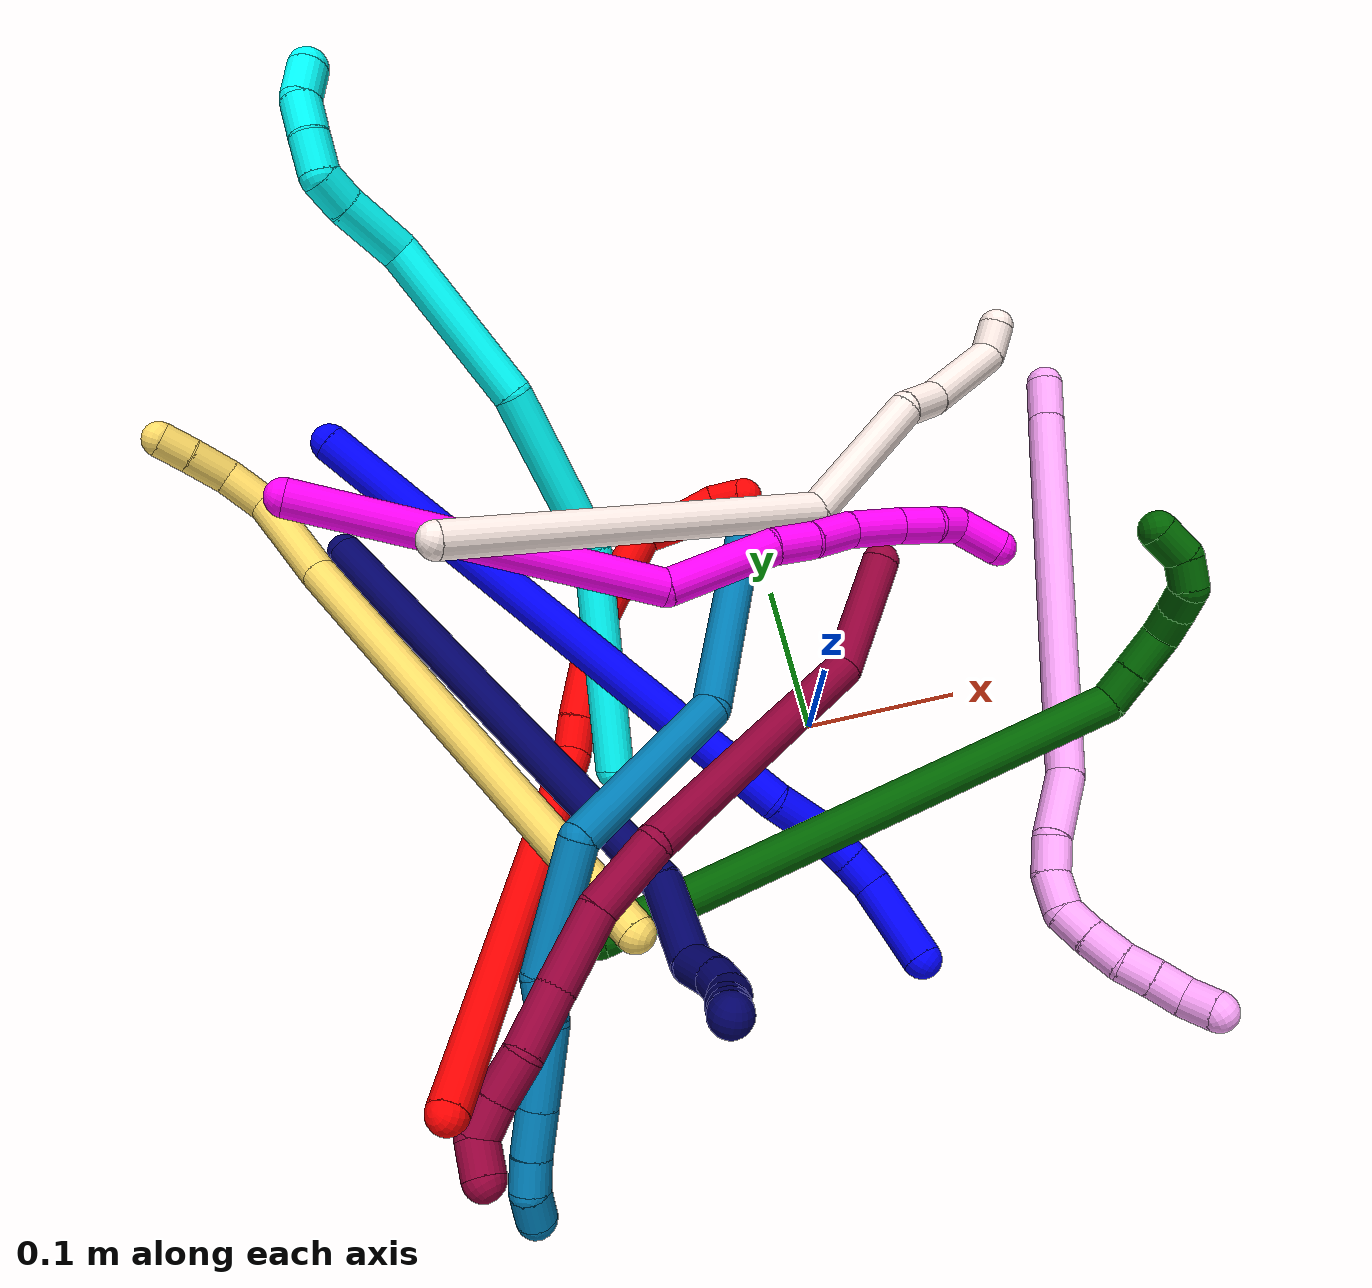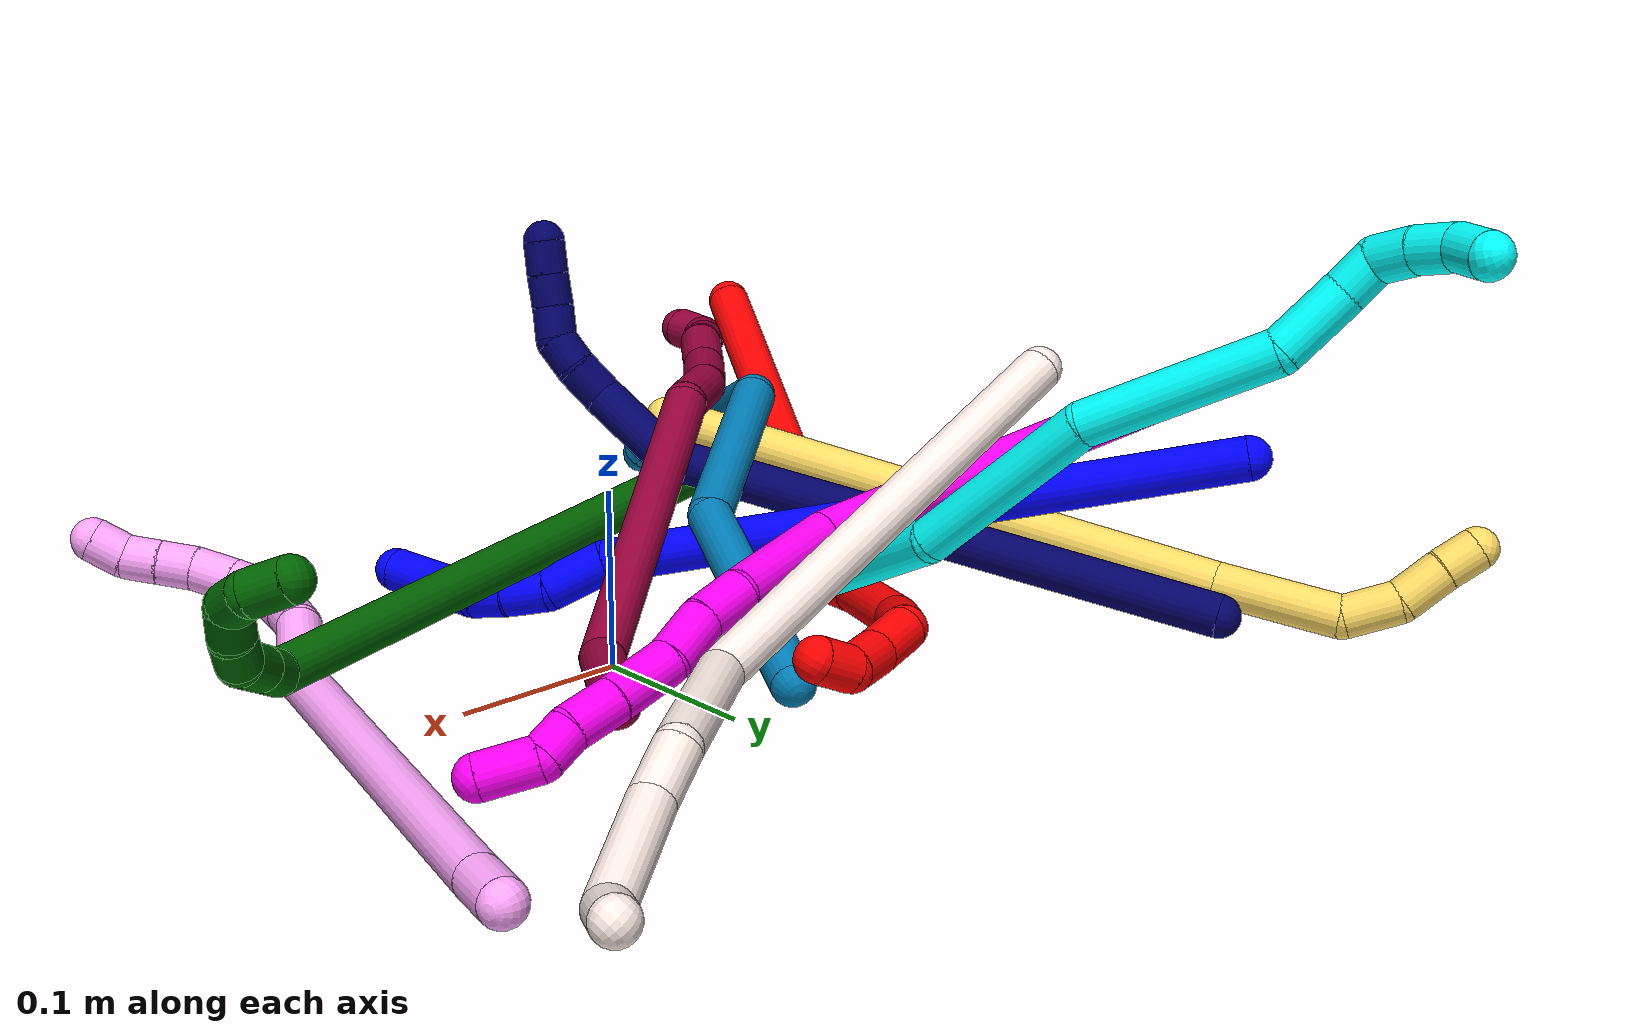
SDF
<sdf version="1.7">
 <world name="default">
  <plugin name="TubeGeneratorPlugin" filename="libtube_generator_plugin.so"/>
  <model name="photoneo_s_sensor">
   <static>1</static>
   <pose>0 0 2 1.57079 1.57079 3.14159</pose>
   <link name="link">
    <inertial><mass>0.1</mass></inertial>
    <sensor name="sensor" type="depth">
     <update_rate>30</update_rate>
     <camera>
      <horizontal_fov>1.22</horizontal_fov>
      <image><width>1920</width><height>1200</height><format>B8G8R8</format></image>
      <clip><near>0.1</near><far>4</far></clip>
      <depth_camera><output>points</output></depth_camera>
     </camera>
     <plugin name="camera_plugin" filename="libgazebo_ros_depth_camera.so">
      <baseline>0.2</baseline>
      <alwaysOn>1</alwaysOn>
      <updateRate>0.0</updateRate>
      <cameraName>camera_ir</cameraName>
      <imageTopicName>/camera/color/image_raw</imageTopicName>
      <cameraInfoTopicName>/camera/color/camera_info</cameraInfoTopicName>
      <depthImageTopicName>/camera/depth/image_raw</depthImageTopicName>
      <depthImageCameraInfoTopicName>/camera/depth/camera_info</depthImageCameraInfoTopicName>
      <pointCloudTopicName>/camera/depth/points</pointCloudTopicName>
      <frameName>fr_optical</frameName>
      <pointCloudCutoff>0.1</pointCloudCutoff>
      <pointCloudCutoffMax>2.0</pointCloudCutoffMax>
      <distortionK1>0</distortionK1>
      <distortionK2>0</distortionK2>
      <distortionK3>0</distortionK3>
      <distortionT1>0</distortionT1>
      <distortionT2>0</distortionT2>
      <CxPrime>0</CxPrime>
      <Cx>0</Cx>
      <Cy>0</Cy>
      <focalLength>0</focalLength>
      <hackBaseline>0</hackBaseline>
     </plugin>
    </sensor>
   </link>
  </model>
  <gravity>0 0 -9.8</gravity>
  <magnetic_field>6e-06 2.3e-05 -4.2e-05</magnetic_field>
  <atmosphere type="adiabatic"/>
  <physics name="default_physics" default="0" type="ode">
   <max_step_size>0.003</max_step_size>
   <real_time_factor>1</real_time_factor>
   <real_time_update_rate>1000</real_time_update_rate>
   <max_contacts>10000</max_contacts>
   <ode>
    <solver>
     <type>quick</type>
     <iters>100</iters>
     <sor>1.3</sor>
     <use_dynamic_moi_rescaling>0</use_dynamic_moi_rescaling>
    </solver>
    <constraints>
     <contact_max_correcting_vel>0</contact_max_correcting_vel>
     <contact_surface_layer>0.001</contact_surface_layer>
     <cfm>0</cfm>
     <erp>0.2</erp>
    </constraints>
   </ode>
  </physics>
  <scene><ambient>0.4 0.4 0.4 1</ambient><background>0.7 0.7 0.7 1</background><shadows>0</shadows></scene>
  <audio><device>default</device></audio>
  <spherical_coordinates>
   <surface_model>EARTH_WGS84</surface_model>
   <latitude_deg>0</latitude_deg>
   <longitude_deg>0</longitude_deg>
   <elevation>0</elevation>
   <heading_deg>0</heading_deg>
  </spherical_coordinates>
  <model name="bin">
   <static>1</static>
   <link name="bottom">
    <collision name="collision-bottom">
     <pose>0 0 -0.01 0 -0 0</pose>
     <geometry><box><size>0.8 0.6 0.02</size></box></geometry>
     <surface>
      <friction><ode><mu>100</mu><mu2>100</mu2></ode></friction>
      <contact><collide_bitmask>65535</collide_bitmask></contact>
     </surface>
    </collision>
   </link>
   <link name="west_wall">
    <collision name="collision-west_wall">
     <pose>-0.41 0 0.1 0 -0 0</pose>
     <geometry><box><size>0.02 0.6 0.2</size></box></geometry>
     <surface>
      <friction><ode><mu>100</mu><mu2>100</mu2></ode></friction>
      <contact><collide_bitmask>65535</collide_bitmask></contact>
     </surface>
    </collision>
   </link>
   <link name="east_wall">
    <collision name="collision-east_wall">
     <pose>0.41 0 0.1 0 -0 0</pose>
     <geometry><box><size>0.02 0.6 0.2</size></box></geometry>
     <surface>
      <friction><ode><mu>100</mu><mu2>100</mu2></ode></friction>
      <contact><collide_bitmask>65535</collide_bitmask></contact>
     </surface>
    </collision>
   </link>
   <link name="south_wall">
    <collision name="collision-south_wall">
     <pose>0 -0.31 0.1 0 -0 0</pose>
     <geometry><box><size>0.8 0.02 0.2</size></box></geometry>
     <surface>
      <friction><ode><mu>100</mu><mu2>100</mu2></ode></friction>
      <contact><collide_bitmask>65535</collide_bitmask></contact>
     </surface>
    </collision>
   </link>
   <link name="north_wall">
    <collision name="collision-north_wall">
     <pose>0 0.31 0.1 0 -0 0</pose>
     <geometry><box><size>0.8 0.02 0.2</size></box></geometry>
     <surface>
      <friction><ode><mu>100</mu><mu2>100</mu2></ode></friction>
      <contact><collide_bitmask>65535</collide_bitmask></contact>
     </surface>
    </collision>
   </link>
  </model>
  <model name="1">
   <static>0</static>
   <link name="1">
    <collision name="collision-cylinder-e_1_1_4">
     <pose>-0.003515 -0.047083 -0.174667 2.87829 -0.01943 -0.146479</pose>
     <geometry><cylinder><radius>0.0125</radius><length>0.361871</length></cylinder></geometry>
     <surface>
      <friction><ode><mu>1.16</mu><mu2>1.16</mu2><slip1>0</slip1><slip2>0</slip2></ode></friction>
      <contact><ode><kp>1e+06</kp><kd>1</kd><max_vel>0</max_vel><min_depth>0.001</min_depth></ode></contact>
     </surface>
    </collision>
    <visual name="visual-cylinder-e_1_1_4">
     <pose>-0.003515 -0.047083 -0.174667 2.87829 -0.01943 -0.146479</pose>
     <geometry><cylinder><radius>0.0125</radius><length>0.361871</length></cylinder></geometry>
     <material><ambient>0 0 1 1</ambient></material>
    </visual>
    <collision name="collision-cylinder-e_2_4_5">
     <pose>-0.010106 -0.103264 -0.364581 2.60363 -0.171505 -0.604573</pose>
     <geometry><cylinder><radius>0.0125</radius><length>0.036039</length></cylinder></geometry>
     <surface>
      <friction><ode><mu>1.16</mu><mu2>1.16</mu2><slip1>0</slip1><slip2>0</slip2></ode></friction>
      <contact><ode><kp>1e+06</kp><kd>1</kd><max_vel>0</max_vel><min_depth>0.001</min_depth></ode></contact>
     </surface>
    </collision>
    <visual name="visual-cylinder-e_2_4_5">
     <pose>-0.010106 -0.103264 -0.364581 2.60363 -0.171505 -0.604573</pose>
     <geometry><cylinder><radius>0.0125</radius><length>0.036039</length></cylinder></geometry>
     <material><ambient>0 0 1 1</ambient></material>
    </visual>
    <collision name="collision-cylinder-e_3_5_6">
     <pose>-0.012085 -0.115712 -0.392285 2.87886 0.084803 0.621414</pose>
     <geometry><cylinder><radius>0.0125</radius><length>0.025893</length></cylinder></geometry>
     <surface>
      <friction><ode><mu>1.16</mu><mu2>1.16</mu2><slip1>0</slip1><slip2>0</slip2></ode></friction>
      <contact><ode><kp>1e+06</kp><kd>1</kd><max_vel>0</max_vel><min_depth>0.001</min_depth></ode></contact>
     </surface>
    </collision>
    <visual name="visual-cylinder-e_3_5_6">
     <pose>-0.012085 -0.115712 -0.392285 2.87886 0.084803 0.621414</pose>
     <geometry><cylinder><radius>0.0125</radius><length>0.025893</length></cylinder></geometry>
     <material><ambient>0 0 1 1</ambient></material>
    </visual>
    <collision name="collision-cylinder-e_4_6_7">
     <pose>-0.00913 -0.12109 -0.414987 2.94616 0.176141 1.46643</pose>
     <geometry><cylinder><radius>0.0125</radius><length>0.021215</length></cylinder></geometry>
     <surface>
      <friction><ode><mu>1.16</mu><mu2>1.16</mu2><slip1>0</slip1><slip2>0</slip2></ode></friction>
      <contact><ode><kp>1e+06</kp><kd>1</kd><max_vel>0</max_vel><min_depth>0.001</min_depth></ode></contact>
     </surface>
    </collision>
    <visual name="visual-cylinder-e_4_6_7">
     <pose>-0.00913 -0.12109 -0.414987 2.94616 0.176141 1.46643</pose>
     <geometry><cylinder><radius>0.0125</radius><length>0.021215</length></cylinder></geometry>
     <material><ambient>0 0 1 1</ambient></material>
    </visual>
    <collision name="collision-cylinder-e_5_7_2">
     <pose>0.002433 -0.120913 -0.450858 -3.05577 0.360748 -2.6791</pose>
     <geometry><cylinder><radius>0.0125</radius><length>0.054983</length></cylinder></geometry>
     <surface>
      <friction><ode><mu>1.16</mu><mu2>1.16</mu2><slip1>0</slip1><slip2>0</slip2></ode></friction>
      <contact><ode><kp>1e+06</kp><kd>1</kd><max_vel>0</max_vel><min_depth>0.001</min_depth></ode></contact>
     </surface>
    </collision>
    <visual name="visual-cylinder-e_5_7_2">
     <pose>0.002433 -0.120913 -0.450858 -3.05577 0.360748 -2.6791</pose>
     <geometry><cylinder><radius>0.0125</radius><length>0.054983</length></cylinder></geometry>
     <material><ambient>0 0 1 1</ambient></material>
    </visual>
    <collision name="collision-sphere-2">
     <pose>0.012137 -0.118708 -0.476485 0 -0 0</pose>
     <geometry><sphere><radius>0.0125</radius></sphere></geometry>
     <surface>
      <friction><ode><mu>1.16</mu><mu2>1.16</mu2><slip1>0</slip1><slip2>0</slip2></ode></friction>
      <contact><ode><kp>1e+06</kp><kd>1</kd><max_vel>0</max_vel><min_depth>0.001</min_depth></ode></contact>
     </surface>
    </collision>
    <visual name="visual-sphere-2">
     <pose>0.012137 -0.118708 -0.476485 0 -0 0</pose>
     <geometry><sphere><radius>0.0125</radius></sphere></geometry>
     <material><ambient>0 0 1 1</ambient></material>
    </visual>
    <collision name="collision-sphere-7">
     <pose>-0.007271 -0.123118 -0.425231 0 -0 0</pose>
     <geometry><sphere><radius>0.0125</radius></sphere></geometry>
     <surface>
      <friction><ode><mu>1.16</mu><mu2>1.16</mu2><slip1>0</slip1><slip2>0</slip2></ode></friction>
      <contact><ode><kp>1e+06</kp><kd>1</kd><max_vel>0</max_vel><min_depth>0.001</min_depth></ode></contact>
     </surface>
    </collision>
    <visual name="visual-sphere-7">
     <pose>-0.007271 -0.123118 -0.425231 0 -0 0</pose>
     <geometry><sphere><radius>0.0125</radius></sphere></geometry>
     <material><ambient>0 0 1 1</ambient></material>
    </visual>
    <collision name="collision-sphere-6">
     <pose>-0.010988 -0.119062 -0.404742 0 -0 0</pose>
     <geometry><sphere><radius>0.0125</radius></sphere></geometry>
     <surface>
      <friction><ode><mu>1.16</mu><mu2>1.16</mu2><slip1>0</slip1><slip2>0</slip2></ode></friction>
      <contact><ode><kp>1e+06</kp><kd>1</kd><max_vel>0</max_vel><min_depth>0.001</min_depth></ode></contact>
     </surface>
    </collision>
    <visual name="visual-sphere-6">
     <pose>-0.010988 -0.119062 -0.404742 0 -0 0</pose>
     <geometry><sphere><radius>0.0125</radius></sphere></geometry>
     <material><ambient>0 0 1 1</ambient></material>
    </visual>
    <collision name="collision-sphere-5">
     <pose>-0.013181 -0.112361 -0.379828 0 -0 0</pose>
     <geometry><sphere><radius>0.0125</radius></sphere></geometry>
     <surface>
      <friction><ode><mu>1.16</mu><mu2>1.16</mu2><slip1>0</slip1><slip2>0</slip2></ode></friction>
      <contact><ode><kp>1e+06</kp><kd>1</kd><max_vel>0</max_vel><min_depth>0.001</min_depth></ode></contact>
     </surface>
    </collision>
    <visual name="visual-sphere-5">
     <pose>-0.013181 -0.112361 -0.379828 0 -0 0</pose>
     <geometry><sphere><radius>0.0125</radius></sphere></geometry>
     <material><ambient>0 0 1 1</ambient></material>
    </visual>
    <collision name="collision-sphere-1">
     <geometry><sphere><radius>0.0125</radius></sphere></geometry>
     <surface>
      <friction><ode><mu>1.16</mu><mu2>1.16</mu2><slip1>0</slip1><slip2>0</slip2></ode></friction>
      <contact><ode><kp>1e+06</kp><kd>1</kd><max_vel>0</max_vel><min_depth>0.001</min_depth></ode></contact>
     </surface>
    </collision>
    <visual name="visual-sphere-1">
     <geometry><sphere><radius>0.0125</radius></sphere></geometry>
     <material><ambient>0 0 1 1</ambient></material>
    </visual>
    <collision name="collision-sphere-4">
     <pose>-0.007031 -0.094166 -0.349334 0 -0 0</pose>
     <geometry><sphere><radius>0.0125</radius></sphere></geometry>
     <surface>
      <friction><ode><mu>1.16</mu><mu2>1.16</mu2><slip1>0</slip1><slip2>0</slip2></ode></friction>
      <contact><ode><kp>1e+06</kp><kd>1</kd><max_vel>0</max_vel><min_depth>0.001</min_depth></ode></contact>
     </surface>
    </collision>
    <visual name="visual-sphere-4">
     <pose>-0.007031 -0.094166 -0.349334 0 -0 0</pose>
     <geometry><sphere><radius>0.0125</radius></sphere></geometry>
     <material><ambient>0 0 1 1</ambient></material>
    </visual>
    <inertial>
     <pose>-0.004018 -0.065945 -0.240193 0 -0 0</pose>
     <mass>0.5</mass>
     <inertia>
      <ixx>0.003329</ixx>
      <ixy>0</ixy>
      <ixz>0</ixz>
      <iyy>-0.004368</iyy>
      <iyz>0</iyz>
      <izz>0.001068</izz>
     </inertia>
    </inertial>
   </link>
   <pose>-0.267252 0.21652 0.112414 1.62135 0.054611 -2.47783</pose>
  </model>
  <model name="2">
   <static>0</static>
   <link name="2">
    <collision name="collision-cylinder-e_1_1_4">
     <pose>0.063696 0.100035 -0.059546 -2.10772 0.500647 -0.845302</pose>
     <geometry><cylinder><radius>0.0125</radius><length>0.265405</length></cylinder></geometry>
     <surface>
      <friction><ode><mu>1.16</mu><mu2>1.16</mu2><slip1>0</slip1><slip2>0</slip2></ode></friction>
      <contact><ode><kp>1e+06</kp><kd>1</kd><max_vel>0</max_vel><min_depth>0.001</min_depth></ode></contact>
     </surface>
    </collision>
    <visual name="visual-cylinder-e_1_1_4">
     <pose>0.063696 0.100035 -0.059546 -2.10772 0.500647 -0.845302</pose>
     <geometry><cylinder><radius>0.0125</radius><length>0.265405</length></cylinder></geometry>
     <material><ambient>1 0 0 1</ambient></material>
    </visual>
    <collision name="collision-cylinder-e_2_4_5">
     <pose>0.136469 0.208275 -0.118118 -1.45256 0.832268 -0.74814</pose>
     <geometry><cylinder><radius>0.0125</radius><length>0.024549</length></cylinder></geometry>
     <surface>
      <friction><ode><mu>1.16</mu><mu2>1.16</mu2><slip1>0</slip1><slip2>0</slip2></ode></friction>
      <contact><ode><kp>1e+06</kp><kd>1</kd><max_vel>0</max_vel><min_depth>0.001</min_depth></ode></contact>
     </surface>
    </collision>
    <visual name="visual-cylinder-e_2_4_5">
     <pose>0.136469 0.208275 -0.118118 -1.45256 0.832268 -0.74814</pose>
     <geometry><cylinder><radius>0.0125</radius><length>0.024549</length></cylinder></geometry>
     <material><ambient>1 0 0 1</ambient></material>
    </visual>
    <collision name="collision-cylinder-e_3_5_6">
     <pose>0.171133 0.238352 -0.11705 -1.56651 0.863544 -0.860293</pose>
     <geometry><cylinder><radius>0.0125</radius><length>0.067324</length></cylinder></geometry>
     <surface>
      <friction><ode><mu>1.16</mu><mu2>1.16</mu2><slip1>0</slip1><slip2>0</slip2></ode></friction>
      <contact><ode><kp>1e+06</kp><kd>1</kd><max_vel>0</max_vel><min_depth>0.001</min_depth></ode></contact>
     </surface>
    </collision>
    <visual name="visual-cylinder-e_3_5_6">
     <pose>0.171133 0.238352 -0.11705 -1.56651 0.863544 -0.860293</pose>
     <geometry><cylinder><radius>0.0125</radius><length>0.067324</length></cylinder></geometry>
     <material><ambient>1 0 0 1</ambient></material>
    </visual>
    <collision name="collision-cylinder-e_4_6_7">
     <pose>0.227193 0.272216 -0.117689 -1.63183 1.1952 -1.25263</pose>
     <geometry><cylinder><radius>0.0125</radius><length>0.065509</length></cylinder></geometry>
     <surface>
      <friction><ode><mu>1.16</mu><mu2>1.16</mu2><slip1>0</slip1><slip2>0</slip2></ode></friction>
      <contact><ode><kp>1e+06</kp><kd>1</kd><max_vel>0</max_vel><min_depth>0.001</min_depth></ode></contact>
     </surface>
    </collision>
    <visual name="visual-cylinder-e_4_6_7">
     <pose>0.227193 0.272216 -0.117689 -1.63183 1.1952 -1.25263</pose>
     <geometry><cylinder><radius>0.0125</radius><length>0.065509</length></cylinder></geometry>
     <material><ambient>1 0 0 1</ambient></material>
    </visual>
    <collision name="collision-cylinder-e_5_7_8">
     <pose>0.268603 0.283851 -0.127273 3.10121 0.890071 3.05695</pose>
     <geometry><cylinder><radius>0.0125</radius><length>0.028153</length></cylinder></geometry>
     <surface>
      <friction><ode><mu>1.16</mu><mu2>1.16</mu2><slip1>0</slip1><slip2>0</slip2></ode></friction>
      <contact><ode><kp>1e+06</kp><kd>1</kd><max_vel>0</max_vel><min_depth>0.001</min_depth></ode></contact>
     </surface>
    </collision>
    <visual name="visual-cylinder-e_5_7_8">
     <pose>0.268603 0.283851 -0.127273 3.10121 0.890071 3.05695</pose>
     <geometry><cylinder><radius>0.0125</radius><length>0.028153</length></cylinder></geometry>
     <material><ambient>1 0 0 1</ambient></material>
    </visual>
    <collision name="collision-cylinder-e_6_8_9">
     <pose>0.291465 0.283615 -0.142492 -3.1226 1.08029 -3.10992</pose>
     <geometry><cylinder><radius>0.0125</radius><length>0.027034</length></cylinder></geometry>
     <surface>
      <friction><ode><mu>1.16</mu><mu2>1.16</mu2><slip1>0</slip1><slip2>0</slip2></ode></friction>
      <contact><ode><kp>1e+06</kp><kd>1</kd><max_vel>0</max_vel><min_depth>0.001</min_depth></ode></contact>
     </surface>
    </collision>
    <visual name="visual-cylinder-e_6_8_9">
     <pose>0.291465 0.283615 -0.142492 -3.1226 1.08029 -3.10992</pose>
     <geometry><cylinder><radius>0.0125</radius><length>0.027034</length></cylinder></geometry>
     <material><ambient>1 0 0 1</ambient></material>
    </visual>
    <collision name="collision-cylinder-e_7_9_2">
     <pose>0.312266 0.277477 -0.150679 1.85388 0.937463 1.18704</pose>
     <geometry><cylinder><radius>0.0125</radius><length>0.022027</length></cylinder></geometry>
     <surface>
      <friction><ode><mu>1.16</mu><mu2>1.16</mu2><slip1>0</slip1><slip2>0</slip2></ode></friction>
      <contact><ode><kp>1e+06</kp><kd>1</kd><max_vel>0</max_vel><min_depth>0.001</min_depth></ode></contact>
     </surface>
    </collision>
    <visual name="visual-cylinder-e_7_9_2">
     <pose>0.312266 0.277477 -0.150679 1.85388 0.937463 1.18704</pose>
     <geometry><cylinder><radius>0.0125</radius><length>0.022027</length></cylinder></geometry>
     <material><ambient>1 0 0 1</ambient></material>
    </visual>
    <collision name="collision-sphere-2">
     <pose>0.321143 0.271218 -0.152499 0 -0 0</pose>
     <geometry><sphere><radius>0.0125</radius></sphere></geometry>
     <surface>
      <friction><ode><mu>1.16</mu><mu2>1.16</mu2><slip1>0</slip1><slip2>0</slip2></ode></friction>
      <contact><ode><kp>1e+06</kp><kd>1</kd><max_vel>0</max_vel><min_depth>0.001</min_depth></ode></contact>
     </surface>
    </collision>
    <visual name="visual-sphere-2">
     <pose>0.321143 0.271218 -0.152499 0 -0 0</pose>
     <geometry><sphere><radius>0.0125</radius></sphere></geometry>
     <material><ambient>1 0 0 1</ambient></material>
    </visual>
    <collision name="collision-sphere-9">
     <pose>0.303389 0.283735 -0.148858 0 -0 0</pose>
     <geometry><sphere><radius>0.0125</radius></sphere></geometry>
     <surface>
      <friction><ode><mu>1.16</mu><mu2>1.16</mu2><slip1>0</slip1><slip2>0</slip2></ode></friction>
      <contact><ode><kp>1e+06</kp><kd>1</kd><max_vel>0</max_vel><min_depth>0.001</min_depth></ode></contact>
     </surface>
    </collision>
    <visual name="visual-sphere-9">
     <pose>0.303389 0.283735 -0.148858 0 -0 0</pose>
     <geometry><sphere><radius>0.0125</radius></sphere></geometry>
     <material><ambient>1 0 0 1</ambient></material>
    </visual>
    <collision name="collision-sphere-4">
     <pose>0.127392 0.200069 -0.119093 0 -0 0</pose>
     <geometry><sphere><radius>0.0125</radius></sphere></geometry>
     <surface>
      <friction><ode><mu>1.16</mu><mu2>1.16</mu2><slip1>0</slip1><slip2>0</slip2></ode></friction>
      <contact><ode><kp>1e+06</kp><kd>1</kd><max_vel>0</max_vel><min_depth>0.001</min_depth></ode></contact>
     </surface>
    </collision>
    <visual name="visual-sphere-4">
     <pose>0.127392 0.200069 -0.119093 0 -0 0</pose>
     <geometry><sphere><radius>0.0125</radius></sphere></geometry>
     <material><ambient>1 0 0 1</ambient></material>
    </visual>
    <collision name="collision-sphere-1">
     <geometry><sphere><radius>0.0125</radius></sphere></geometry>
     <surface>
      <friction><ode><mu>1.16</mu><mu2>1.16</mu2><slip1>0</slip1><slip2>0</slip2></ode></friction>
      <contact><ode><kp>1e+06</kp><kd>1</kd><max_vel>0</max_vel><min_depth>0.001</min_depth></ode></contact>
     </surface>
    </collision>
    <visual name="visual-sphere-1">
     <geometry><sphere><radius>0.0125</radius></sphere></geometry>
     <material><ambient>1 0 0 1</ambient></material>
    </visual>
    <collision name="collision-sphere-8">
     <pose>0.279542 0.283494 -0.136125 0 -0 0</pose>
     <geometry><sphere><radius>0.0125</radius></sphere></geometry>
     <surface>
      <friction><ode><mu>1.16</mu><mu2>1.16</mu2><slip1>0</slip1><slip2>0</slip2></ode></friction>
      <contact><ode><kp>1e+06</kp><kd>1</kd><max_vel>0</max_vel><min_depth>0.001</min_depth></ode></contact>
     </surface>
    </collision>
    <visual name="visual-sphere-8">
     <pose>0.279542 0.283494 -0.136125 0 -0 0</pose>
     <geometry><sphere><radius>0.0125</radius></sphere></geometry>
     <material><ambient>1 0 0 1</ambient></material>
    </visual>
    <collision name="collision-sphere-5">
     <pose>0.145545 0.21648 -0.117143 0 -0 0</pose>
     <geometry><sphere><radius>0.0125</radius></sphere></geometry>
     <surface>
      <friction><ode><mu>1.16</mu><mu2>1.16</mu2><slip1>0</slip1><slip2>0</slip2></ode></friction>
      <contact><ode><kp>1e+06</kp><kd>1</kd><max_vel>0</max_vel><min_depth>0.001</min_depth></ode></contact>
     </surface>
    </collision>
    <visual name="visual-sphere-5">
     <pose>0.145545 0.21648 -0.117143 0 -0 0</pose>
     <geometry><sphere><radius>0.0125</radius></sphere></geometry>
     <material><ambient>1 0 0 1</ambient></material>
    </visual>
    <collision name="collision-sphere-6">
     <pose>0.196722 0.260223 -0.116956 0 -0 0</pose>
     <geometry><sphere><radius>0.0125</radius></sphere></geometry>
     <surface>
      <friction><ode><mu>1.16</mu><mu2>1.16</mu2><slip1>0</slip1><slip2>0</slip2></ode></friction>
      <contact><ode><kp>1e+06</kp><kd>1</kd><max_vel>0</max_vel><min_depth>0.001</min_depth></ode></contact>
     </surface>
    </collision>
    <visual name="visual-sphere-6">
     <pose>0.196722 0.260223 -0.116956 0 -0 0</pose>
     <geometry><sphere><radius>0.0125</radius></sphere></geometry>
     <material><ambient>1 0 0 1</ambient></material>
    </visual>
    <collision name="collision-sphere-7">
     <pose>0.257664 0.284209 -0.118422 0 -0 0</pose>
     <geometry><sphere><radius>0.0125</radius></sphere></geometry>
     <surface>
      <friction><ode><mu>1.16</mu><mu2>1.16</mu2><slip1>0</slip1><slip2>0</slip2></ode></friction>
      <contact><ode><kp>1e+06</kp><kd>1</kd><max_vel>0</max_vel><min_depth>0.001</min_depth></ode></contact>
     </surface>
    </collision>
    <visual name="visual-sphere-7">
     <pose>0.257664 0.284209 -0.118422 0 -0 0</pose>
     <geometry><sphere><radius>0.0125</radius></sphere></geometry>
     <material><ambient>1 0 0 1</ambient></material>
    </visual>
    <inertial>
     <pose>0.137959 0.174625 -0.090095 0 -0 0</pose>
     <mass>0.5</mass>
     <inertia>
      <ixx>-0.000101</ixx>
      <ixy>0</ixy>
      <ixz>0</ixz>
      <iyy>-0.001033</iyy>
      <iyz>0</iyz>
      <izz>-0.002028</izz>
     </inertia>
    </inertial>
   </link>
   <pose>-0.264702 -0.205137 0.120935 -0.392051 -0.4656 0.499255</pose>
  </model>
  <model name="3">
   <static>0</static>
   <link name="3">
    <collision name="collision-cylinder-e_1_1_4">
     <pose>-0.013373 0.012123 0.069575 -0.172514 -0.187147 0.01623</pose>
     <geometry><cylinder><radius>0.0125</radius><length>0.143756</length></cylinder></geometry>
     <surface>
      <friction><ode><mu>1.16</mu><mu2>1.16</mu2><slip1>0</slip1><slip2>0</slip2></ode></friction>
      <contact><ode><kp>1e+06</kp><kd>1</kd><max_vel>0</max_vel><min_depth>0.001</min_depth></ode></contact>
     </surface>
    </collision>
    <visual name="visual-cylinder-e_1_1_4">
     <pose>-0.013373 0.012123 0.069575 -0.172514 -0.187147 0.01623</pose>
     <geometry><cylinder><radius>0.0125</radius><length>0.143756</length></cylinder></geometry>
     <material><ambient>0.003922 1 0.996078 1</ambient></material>
    </visual>
    <collision name="collision-cylinder-e_2_4_5">
     <pose>-0.015214 0.048175 0.188382 -0.452419 0.207654 -0.047955</pose>
     <geometry><cylinder><radius>0.0125</radius><length>0.111882</length></cylinder></geometry>
     <surface>
      <friction><ode><mu>1.16</mu><mu2>1.16</mu2><slip1>0</slip1><slip2>0</slip2></ode></friction>
      <contact><ode><kp>1e+06</kp><kd>1</kd><max_vel>0</max_vel><min_depth>0.001</min_depth></ode></contact>
     </surface>
    </collision>
    <visual name="visual-cylinder-e_2_4_5">
     <pose>-0.015214 0.048175 0.188382 -0.452419 0.207654 -0.047955</pose>
     <geometry><cylinder><radius>0.0125</radius><length>0.111882</length></cylinder></geometry>
     <material><ambient>0.003922 1 0.996078 1</ambient></material>
    </visual>
    <collision name="collision-cylinder-e_3_5_6">
     <pose>0.016789 0.081293 0.287286 -0.182925 0.385002 -0.035751</pose>
     <geometry><cylinder><radius>0.0125</radius><length>0.109009</length></cylinder></geometry>
     <surface>
      <friction><ode><mu>1.16</mu><mu2>1.16</mu2><slip1>0</slip1><slip2>0</slip2></ode></friction>
      <contact><ode><kp>1e+06</kp><kd>1</kd><max_vel>0</max_vel><min_depth>0.001</min_depth></ode></contact>
     </surface>
    </collision>
    <visual name="visual-cylinder-e_3_5_6">
     <pose>0.016789 0.081293 0.287286 -0.182925 0.385002 -0.035751</pose>
     <geometry><cylinder><radius>0.0125</radius><length>0.109009</length></cylinder></geometry>
     <material><ambient>0.003922 1 0.996078 1</ambient></material>
    </visual>
    <collision name="collision-cylinder-e_4_6_7">
     <pose>0.048951 0.101656 0.350775 -0.679989 0.581976 -0.21109</pose>
     <geometry><cylinder><radius>0.0125</radius><length>0.042544</length></cylinder></geometry>
     <surface>
      <friction><ode><mu>1.16</mu><mu2>1.16</mu2><slip1>0</slip1><slip2>0</slip2></ode></friction>
      <contact><ode><kp>1e+06</kp><kd>1</kd><max_vel>0</max_vel><min_depth>0.001</min_depth></ode></contact>
     </surface>
    </collision>
    <visual name="visual-cylinder-e_4_6_7">
     <pose>0.048951 0.101656 0.350775 -0.679989 0.581976 -0.21109</pose>
     <geometry><cylinder><radius>0.0125</radius><length>0.042544</length></cylinder></geometry>
     <material><ambient>0.003922 1 0.996078 1</ambient></material>
    </visual>
    <collision name="collision-cylinder-e_5_7_8">
     <pose>0.065178 0.118862 0.372218 -0.669343 0.436348 -0.153891</pose>
     <geometry><cylinder><radius>0.0125</radius><length>0.021457</length></cylinder></geometry>
     <surface>
      <friction><ode><mu>1.16</mu><mu2>1.16</mu2><slip1>0</slip1><slip2>0</slip2></ode></friction>
      <contact><ode><kp>1e+06</kp><kd>1</kd><max_vel>0</max_vel><min_depth>0.001</min_depth></ode></contact>
     </surface>
    </collision>
    <visual name="visual-cylinder-e_5_7_8">
     <pose>0.065178 0.118862 0.372218 -0.669343 0.436348 -0.153891</pose>
     <geometry><cylinder><radius>0.0125</radius><length>0.021457</length></cylinder></geometry>
     <material><ambient>0.003922 1 0.996078 1</ambient></material>
    </visual>
    <collision name="collision-cylinder-e_6_8_9">
     <pose>0.069281 0.125624 0.392035 -0.059708 -0.035286 0.001054</pose>
     <geometry><cylinder><radius>0.0125</radius><length>0.024444</length></cylinder></geometry>
     <surface>
      <friction><ode><mu>1.16</mu><mu2>1.16</mu2><slip1>0</slip1><slip2>0</slip2></ode></friction>
      <contact><ode><kp>1e+06</kp><kd>1</kd><max_vel>0</max_vel><min_depth>0.001</min_depth></ode></contact>
     </surface>
    </collision>
    <visual name="visual-cylinder-e_6_8_9">
     <pose>0.069281 0.125624 0.392035 -0.059708 -0.035286 0.001054</pose>
     <geometry><cylinder><radius>0.0125</radius><length>0.024444</length></cylinder></geometry>
     <material><ambient>0.003922 1 0.996078 1</ambient></material>
    </visual>
    <collision name="collision-cylinder-e_7_9_10">
     <pose>0.06825 0.12542 0.415773 0.080615 -0.051734 -0.002087</pose>
     <geometry><cylinder><radius>0.0125</radius><length>0.023196</length></cylinder></geometry>
     <surface>
      <friction><ode><mu>1.16</mu><mu2>1.16</mu2><slip1>0</slip1><slip2>0</slip2></ode></friction>
      <contact><ode><kp>1e+06</kp><kd>1</kd><max_vel>0</max_vel><min_depth>0.001</min_depth></ode></contact>
     </surface>
    </collision>
    <visual name="visual-cylinder-e_7_9_10">
     <pose>0.06825 0.12542 0.415773 0.080615 -0.051734 -0.002087</pose>
     <geometry><cylinder><radius>0.0125</radius><length>0.023196</length></cylinder></geometry>
     <material><ambient>0.003922 1 0.996078 1</ambient></material>
    </visual>
    <collision name="collision-cylinder-e_8_10_2">
     <pose>0.062792 0.121627 0.437748 0.26767 -0.422232 -0.057693</pose>
     <geometry><cylinder><radius>0.0125</radius><length>0.023712</length></cylinder></geometry>
     <surface>
      <friction><ode><mu>1.16</mu><mu2>1.16</mu2><slip1>0</slip1><slip2>0</slip2></ode></friction>
      <contact><ode><kp>1e+06</kp><kd>1</kd><max_vel>0</max_vel><min_depth>0.001</min_depth></ode></contact>
     </surface>
    </collision>
    <visual name="visual-cylinder-e_8_10_2">
     <pose>0.062792 0.121627 0.437748 0.26767 -0.422232 -0.057693</pose>
     <geometry><cylinder><radius>0.0125</radius><length>0.023712</length></cylinder></geometry>
     <material><ambient>0.003922 1 0.996078 1</ambient></material>
    </visual>
    <collision name="collision-sphere-2">
     <pose>0.057933 0.118767 0.448177 0 -0 0</pose>
     <geometry><sphere><radius>0.0125</radius></sphere></geometry>
     <surface>
      <friction><ode><mu>1.16</mu><mu2>1.16</mu2><slip1>0</slip1><slip2>0</slip2></ode></friction>
      <contact><ode><kp>1e+06</kp><kd>1</kd><max_vel>0</max_vel><min_depth>0.001</min_depth></ode></contact>
     </surface>
    </collision>
    <visual name="visual-sphere-2">
     <pose>0.057933 0.118767 0.448177 0 -0 0</pose>
     <geometry><sphere><radius>0.0125</radius></sphere></geometry>
     <material><ambient>0.003922 1 0.996078 1</ambient></material>
    </visual>
    <collision name="collision-sphere-10">
     <pose>0.067651 0.124487 0.427318 0 -0 0</pose>
     <geometry><sphere><radius>0.0125</radius></sphere></geometry>
     <surface>
      <friction><ode><mu>1.16</mu><mu2>1.16</mu2><slip1>0</slip1><slip2>0</slip2></ode></friction>
      <contact><ode><kp>1e+06</kp><kd>1</kd><max_vel>0</max_vel><min_depth>0.001</min_depth></ode></contact>
     </surface>
    </collision>
    <visual name="visual-sphere-10">
     <pose>0.067651 0.124487 0.427318 0 -0 0</pose>
     <geometry><sphere><radius>0.0125</radius></sphere></geometry>
     <material><ambient>0.003922 1 0.996078 1</ambient></material>
    </visual>
    <collision name="collision-sphere-9">
     <pose>0.06885 0.126353 0.404228 0 -0 0</pose>
     <geometry><sphere><radius>0.0125</radius></sphere></geometry>
     <surface>
      <friction><ode><mu>1.16</mu><mu2>1.16</mu2><slip1>0</slip1><slip2>0</slip2></ode></friction>
      <contact><ode><kp>1e+06</kp><kd>1</kd><max_vel>0</max_vel><min_depth>0.001</min_depth></ode></contact>
     </surface>
    </collision>
    <visual name="visual-sphere-9">
     <pose>0.06885 0.126353 0.404228 0 -0 0</pose>
     <geometry><sphere><radius>0.0125</radius></sphere></geometry>
     <material><ambient>0.003922 1 0.996078 1</ambient></material>
    </visual>
    <collision name="collision-sphere-4">
     <pose>-0.026747 0.024246 0.13915 0 -0 0</pose>
     <geometry><sphere><radius>0.0125</radius></sphere></geometry>
     <surface>
      <friction><ode><mu>1.16</mu><mu2>1.16</mu2><slip1>0</slip1><slip2>0</slip2></ode></friction>
      <contact><ode><kp>1e+06</kp><kd>1</kd><max_vel>0</max_vel><min_depth>0.001</min_depth></ode></contact>
     </surface>
    </collision>
    <visual name="visual-sphere-4">
     <pose>-0.026747 0.024246 0.13915 0 -0 0</pose>
     <geometry><sphere><radius>0.0125</radius></sphere></geometry>
     <material><ambient>0.003922 1 0.996078 1</ambient></material>
    </visual>
    <collision name="collision-sphere-1">
     <geometry><sphere><radius>0.0125</radius></sphere></geometry>
     <surface>
      <friction><ode><mu>1.16</mu><mu2>1.16</mu2><slip1>0</slip1><slip2>0</slip2></ode></friction>
      <contact><ode><kp>1e+06</kp><kd>1</kd><max_vel>0</max_vel><min_depth>0.001</min_depth></ode></contact>
     </surface>
    </collision>
    <visual name="visual-sphere-1">
     <geometry><sphere><radius>0.0125</radius></sphere></geometry>
     <material><ambient>0.003922 1 0.996078 1</ambient></material>
    </visual>
    <collision name="collision-sphere-8">
     <pose>0.069712 0.124895 0.379843 0 -0 0</pose>
     <geometry><sphere><radius>0.0125</radius></sphere></geometry>
     <surface>
      <friction><ode><mu>1.16</mu><mu2>1.16</mu2><slip1>0</slip1><slip2>0</slip2></ode></friction>
      <contact><ode><kp>1e+06</kp><kd>1</kd><max_vel>0</max_vel><min_depth>0.001</min_depth></ode></contact>
     </surface>
    </collision>
    <visual name="visual-sphere-8">
     <pose>0.069712 0.124895 0.379843 0 -0 0</pose>
     <geometry><sphere><radius>0.0125</radius></sphere></geometry>
     <material><ambient>0.003922 1 0.996078 1</ambient></material>
    </visual>
    <collision name="collision-sphere-5">
     <pose>-0.003681 0.072104 0.237614 0 -0 0</pose>
     <geometry><sphere><radius>0.0125</radius></sphere></geometry>
     <surface>
      <friction><ode><mu>1.16</mu><mu2>1.16</mu2><slip1>0</slip1><slip2>0</slip2></ode></friction>
      <contact><ode><kp>1e+06</kp><kd>1</kd><max_vel>0</max_vel><min_depth>0.001</min_depth></ode></contact>
     </surface>
    </collision>
    <visual name="visual-sphere-5">
     <pose>-0.003681 0.072104 0.237614 0 -0 0</pose>
     <geometry><sphere><radius>0.0125</radius></sphere></geometry>
     <material><ambient>0.003922 1 0.996078 1</ambient></material>
    </visual>
    <collision name="collision-sphere-6">
     <pose>0.037259 0.090482 0.336957 0 -0 0</pose>
     <geometry><sphere><radius>0.0125</radius></sphere></geometry>
     <surface>
      <friction><ode><mu>1.16</mu><mu2>1.16</mu2><slip1>0</slip1><slip2>0</slip2></ode></friction>
      <contact><ode><kp>1e+06</kp><kd>1</kd><max_vel>0</max_vel><min_depth>0.001</min_depth></ode></contact>
     </surface>
    </collision>
    <visual name="visual-sphere-6">
     <pose>0.037259 0.090482 0.336957 0 -0 0</pose>
     <geometry><sphere><radius>0.0125</radius></sphere></geometry>
     <material><ambient>0.003922 1 0.996078 1</ambient></material>
    </visual>
    <collision name="collision-sphere-7">
     <pose>0.060644 0.112829 0.364593 0 -0 0</pose>
     <geometry><sphere><radius>0.0125</radius></sphere></geometry>
     <surface>
      <friction><ode><mu>1.16</mu><mu2>1.16</mu2><slip1>0</slip1><slip2>0</slip2></ode></friction>
      <contact><ode><kp>1e+06</kp><kd>1</kd><max_vel>0</max_vel><min_depth>0.001</min_depth></ode></contact>
     </surface>
    </collision>
    <visual name="visual-sphere-7">
     <pose>0.060644 0.112829 0.364593 0 -0 0</pose>
     <geometry><sphere><radius>0.0125</radius></sphere></geometry>
     <material><ambient>0.003922 1 0.996078 1</ambient></material>
    </visual>
    <inertial>
     <pose>0.012904 0.063467 0.229824 0 -0 0</pose>
     <mass>0.5</mass>
     <inertia>
      <ixx>0.000482</ixx>
      <ixy>0</ixy>
      <ixz>0</ixz>
      <iyy>0.000486</iyy>
      <iyz>0</iyz>
      <izz>-0.000107</izz>
     </inertia>
    </inertial>
   </link>
   <pose>-0.132883 -0.003558 0.011492 1.26501 0.0119 -3.05309</pose>
  </model>
  <model name="4">
   <static>0</static>
   <link name="4">
    <collision name="collision-cylinder-e_1_1_4">
     <pose>-0.004162 -0.011198 -0.00917 2.25696 -0.279977 -0.578366</pose>
     <geometry><cylinder><radius>0.0125</radius><length>0.03012</length></cylinder></geometry>
     <surface>
      <friction><ode><mu>1.16</mu><mu2>1.16</mu2><slip1>0</slip1><slip2>0</slip2></ode></friction>
      <contact><ode><kp>1e+06</kp><kd>1</kd><max_vel>0</max_vel><min_depth>0.001</min_depth></ode></contact>
     </surface>
    </collision>
    <visual name="visual-cylinder-e_1_1_4">
     <pose>-0.004162 -0.011198 -0.00917 2.25696 -0.279977 -0.578366</pose>
     <geometry><cylinder><radius>0.0125</radius><length>0.03012</length></cylinder></geometry>
     <material><ambient>1 0.65098 0.996078 1</ambient></material>
    </visual>
    <collision name="collision-cylinder-e_2_4_5">
     <pose>-0.049833 -0.119477 -0.099724 2.26846 -0.316647 -0.659387</pose>
     <geometry><cylinder><radius>0.0125</radius><length>0.266617</length></cylinder></geometry>
     <surface>
      <friction><ode><mu>1.16</mu><mu2>1.16</mu2><slip1>0</slip1><slip2>0</slip2></ode></friction>
      <contact><ode><kp>1e+06</kp><kd>1</kd><max_vel>0</max_vel><min_depth>0.001</min_depth></ode></contact>
     </surface>
    </collision>
    <visual name="visual-cylinder-e_2_4_5">
     <pose>-0.049833 -0.119477 -0.099724 2.26846 -0.316647 -0.659387</pose>
     <geometry><cylinder><radius>0.0125</radius><length>0.266617</length></cylinder></geometry>
     <material><ambient>1 0.65098 0.996078 1</ambient></material>
    </visual>
    <collision name="collision-cylinder-e_3_5_6">
     <pose>-0.102844 -0.227189 -0.200248 2.63463 -0.483692 -1.52185</pose>
     <geometry><cylinder><radius>0.0125</radius><length>0.049461</length></cylinder></geometry>
     <surface>
      <friction><ode><mu>1.16</mu><mu2>1.16</mu2><slip1>0</slip1><slip2>0</slip2></ode></friction>
      <contact><ode><kp>1e+06</kp><kd>1</kd><max_vel>0</max_vel><min_depth>0.001</min_depth></ode></contact>
     </surface>
    </collision>
    <visual name="visual-cylinder-e_3_5_6">
     <pose>-0.102844 -0.227189 -0.200248 2.63463 -0.483692 -1.52185</pose>
     <geometry><cylinder><radius>0.0125</radius><length>0.049461</length></cylinder></geometry>
     <material><ambient>1 0.65098 0.996078 1</ambient></material>
    </visual>
    <collision name="collision-cylinder-e_4_6_7">
     <pose>-0.117365 -0.246194 -0.227201 2.3215 -0.25778 -0.579547</pose>
     <geometry><cylinder><radius>0.0125</radius><length>0.02369</length></cylinder></geometry>
     <surface>
      <friction><ode><mu>1.16</mu><mu2>1.16</mu2><slip1>0</slip1><slip2>0</slip2></ode></friction>
      <contact><ode><kp>1e+06</kp><kd>1</kd><max_vel>0</max_vel><min_depth>0.001</min_depth></ode></contact>
     </surface>
    </collision>
    <visual name="visual-cylinder-e_4_6_7">
     <pose>-0.117365 -0.246194 -0.227201 2.3215 -0.25778 -0.579547</pose>
     <geometry><cylinder><radius>0.0125</radius><length>0.02369</length></cylinder></geometry>
     <material><ambient>1 0.65098 0.996078 1</ambient></material>
    </visual>
    <collision name="collision-cylinder-e_5_7_8">
     <pose>-0.127053 -0.263875 -0.240199 2.07908 -0.55931 -0.909183</pose>
     <geometry><cylinder><radius>0.0125</radius><length>0.025137</length></cylinder></geometry>
     <surface>
      <friction><ode><mu>1.16</mu><mu2>1.16</mu2><slip1>0</slip1><slip2>0</slip2></ode></friction>
      <contact><ode><kp>1e+06</kp><kd>1</kd><max_vel>0</max_vel><min_depth>0.001</min_depth></ode></contact>
     </surface>
    </collision>
    <visual name="visual-cylinder-e_5_7_8">
     <pose>-0.127053 -0.263875 -0.240199 2.07908 -0.55931 -0.909183</pose>
     <geometry><cylinder><radius>0.0125</radius><length>0.025137</length></cylinder></geometry>
     <material><ambient>1 0.65098 0.996078 1</ambient></material>
    </visual>
    <collision name="collision-cylinder-e_6_8_9">
     <pose>-0.139417 -0.281896 -0.244267 1.44339 -0.575103 -0.509258</pose>
     <geometry><cylinder><radius>0.0125</radius><length>0.02094</length></cylinder></geometry>
     <surface>
      <friction><ode><mu>1.16</mu><mu2>1.16</mu2><slip1>0</slip1><slip2>0</slip2></ode></friction>
      <contact><ode><kp>1e+06</kp><kd>1</kd><max_vel>0</max_vel><min_depth>0.001</min_depth></ode></contact>
     </surface>
    </collision>
    <visual name="visual-cylinder-e_6_8_9">
     <pose>-0.139417 -0.281896 -0.244267 1.44339 -0.575103 -0.509258</pose>
     <geometry><cylinder><radius>0.0125</radius><length>0.02094</length></cylinder></geometry>
     <material><ambient>1 0.65098 0.996078 1</ambient></material>
    </visual>
    <collision name="collision-cylinder-e_7_9_10">
     <pose>-0.151477 -0.300409 -0.240886 1.34366 -0.564271 -0.453114</pose>
     <geometry><cylinder><radius>0.0125</radius><length>0.023803</length></cylinder></geometry>
     <surface>
      <friction><ode><mu>1.16</mu><mu2>1.16</mu2><slip1>0</slip1><slip2>0</slip2></ode></friction>
      <contact><ode><kp>1e+06</kp><kd>1</kd><max_vel>0</max_vel><min_depth>0.001</min_depth></ode></contact>
     </surface>
    </collision>
    <visual name="visual-cylinder-e_7_9_10">
     <pose>-0.151477 -0.300409 -0.240886 1.34366 -0.564271 -0.453114</pose>
     <geometry><cylinder><radius>0.0125</radius><length>0.023803</length></cylinder></geometry>
     <material><ambient>1 0.65098 0.996078 1</ambient></material>
    </visual>
    <collision name="collision-cylinder-e_8_10_11">
     <pose>-0.162426 -0.318262 -0.234698 1.11753 -0.472915 -0.29907</pose>
     <geometry><cylinder><radius>0.0125</radius><length>0.020127</length></cylinder></geometry>
     <surface>
      <friction><ode><mu>1.16</mu><mu2>1.16</mu2><slip1>0</slip1><slip2>0</slip2></ode></friction>
      <contact><ode><kp>1e+06</kp><kd>1</kd><max_vel>0</max_vel><min_depth>0.001</min_depth></ode></contact>
     </surface>
    </collision>
    <visual name="visual-cylinder-e_8_10_11">
     <pose>-0.162426 -0.318262 -0.234698 1.11753 -0.472915 -0.29907</pose>
     <geometry><cylinder><radius>0.0125</radius><length>0.020127</length></cylinder></geometry>
     <material><ambient>1 0.65098 0.996078 1</ambient></material>
    </visual>
    <collision name="collision-cylinder-e_9_11_12">
     <pose>-0.171468 -0.334571 -0.227298 1.17215 -0.461872 -0.3097</pose>
     <geometry><cylinder><radius>0.0125</radius><length>0.020011</length></cylinder></geometry>
     <surface>
      <friction><ode><mu>1.16</mu><mu2>1.16</mu2><slip1>0</slip1><slip2>0</slip2></ode></friction>
      <contact><ode><kp>1e+06</kp><kd>1</kd><max_vel>0</max_vel><min_depth>0.001</min_depth></ode></contact>
     </surface>
    </collision>
    <visual name="visual-cylinder-e_9_11_12">
     <pose>-0.171468 -0.334571 -0.227298 1.17215 -0.461872 -0.3097</pose>
     <geometry><cylinder><radius>0.0125</radius><length>0.020011</length></cylinder></geometry>
     <material><ambient>1 0.65098 0.996078 1</ambient></material>
    </visual>
    <collision name="collision-cylinder-e_10_12_2">
     <pose>-0.183145 -0.348868 -0.22031 1.04433 -0.801518 -0.478284</pose>
     <geometry><cylinder><radius>0.0125</radius><length>0.020092</length></cylinder></geometry>
     <surface>
      <friction><ode><mu>1.16</mu><mu2>1.16</mu2><slip1>0</slip1><slip2>0</slip2></ode></friction>
      <contact><ode><kp>1e+06</kp><kd>1</kd><max_vel>0</max_vel><min_depth>0.001</min_depth></ode></contact>
     </surface>
    </collision>
    <visual name="visual-cylinder-e_10_12_2">
     <pose>-0.183145 -0.348868 -0.22031 1.04433 -0.801518 -0.478284</pose>
     <geometry><cylinder><radius>0.0125</radius><length>0.020092</length></cylinder></geometry>
     <material><ambient>1 0.65098 0.996078 1</ambient></material>
    </visual>
    <collision name="collision-sphere-2">
     <pose>-0.190362 -0.35491 -0.216798 0 -0 0</pose>
     <geometry><sphere><radius>0.0125</radius></sphere></geometry>
     <surface>
      <friction><ode><mu>1.16</mu><mu2>1.16</mu2><slip1>0</slip1><slip2>0</slip2></ode></friction>
      <contact><ode><kp>1e+06</kp><kd>1</kd><max_vel>0</max_vel><min_depth>0.001</min_depth></ode></contact>
     </surface>
    </collision>
    <visual name="visual-sphere-2">
     <pose>-0.190362 -0.35491 -0.216798 0 -0 0</pose>
     <geometry><sphere><radius>0.0125</radius></sphere></geometry>
     <material><ambient>1 0.65098 0.996078 1</ambient></material>
    </visual>
    <collision name="collision-sphere-12">
     <pose>-0.175927 -0.342826 -0.223821 0 -0 0</pose>
     <geometry><sphere><radius>0.0125</radius></sphere></geometry>
     <surface>
      <friction><ode><mu>1.16</mu><mu2>1.16</mu2><slip1>0</slip1><slip2>0</slip2></ode></friction>
      <contact><ode><kp>1e+06</kp><kd>1</kd><max_vel>0</max_vel><min_depth>0.001</min_depth></ode></contact>
     </surface>
    </collision>
    <visual name="visual-sphere-12">
     <pose>-0.175927 -0.342826 -0.223821 0 -0 0</pose>
     <geometry><sphere><radius>0.0125</radius></sphere></geometry>
     <material><ambient>1 0.65098 0.996078 1</ambient></material>
    </visual>
    <collision name="collision-sphere-11">
     <pose>-0.16701 -0.326316 -0.230775 0 -0 0</pose>
     <geometry><sphere><radius>0.0125</radius></sphere></geometry>
     <surface>
      <friction><ode><mu>1.16</mu><mu2>1.16</mu2><slip1>0</slip1><slip2>0</slip2></ode></friction>
      <contact><ode><kp>1e+06</kp><kd>1</kd><max_vel>0</max_vel><min_depth>0.001</min_depth></ode></contact>
     </surface>
    </collision>
    <visual name="visual-sphere-11">
     <pose>-0.16701 -0.326316 -0.230775 0 -0 0</pose>
     <geometry><sphere><radius>0.0125</radius></sphere></geometry>
     <material><ambient>1 0.65098 0.996078 1</ambient></material>
    </visual>
    <collision name="collision-sphere-10">
     <pose>-0.157842 -0.310207 -0.238621 0 -0 0</pose>
     <geometry><sphere><radius>0.0125</radius></sphere></geometry>
     <surface>
      <friction><ode><mu>1.16</mu><mu2>1.16</mu2><slip1>0</slip1><slip2>0</slip2></ode></friction>
      <contact><ode><kp>1e+06</kp><kd>1</kd><max_vel>0</max_vel><min_depth>0.001</min_depth></ode></contact>
     </surface>
    </collision>
    <visual name="visual-sphere-10">
     <pose>-0.157842 -0.310207 -0.238621 0 -0 0</pose>
     <geometry><sphere><radius>0.0125</radius></sphere></geometry>
     <material><ambient>1 0.65098 0.996078 1</ambient></material>
    </visual>
    <collision name="collision-sphere-9">
     <pose>-0.145112 -0.290611 -0.243151 0 -0 0</pose>
     <geometry><sphere><radius>0.0125</radius></sphere></geometry>
     <surface>
      <friction><ode><mu>1.16</mu><mu2>1.16</mu2><slip1>0</slip1><slip2>0</slip2></ode></friction>
      <contact><ode><kp>1e+06</kp><kd>1</kd><max_vel>0</max_vel><min_depth>0.001</min_depth></ode></contact>
     </surface>
    </collision>
    <visual name="visual-sphere-9">
     <pose>-0.145112 -0.290611 -0.243151 0 -0 0</pose>
     <geometry><sphere><radius>0.0125</radius></sphere></geometry>
     <material><ambient>1 0.65098 0.996078 1</ambient></material>
    </visual>
    <collision name="collision-sphere-4">
     <pose>-0.008323 -0.022396 -0.01834 0 -0 0</pose>
     <geometry><sphere><radius>0.0125</radius></sphere></geometry>
     <surface>
      <friction><ode><mu>1.16</mu><mu2>1.16</mu2><slip1>0</slip1><slip2>0</slip2></ode></friction>
      <contact><ode><kp>1e+06</kp><kd>1</kd><max_vel>0</max_vel><min_depth>0.001</min_depth></ode></contact>
     </surface>
    </collision>
    <visual name="visual-sphere-4">
     <pose>-0.008323 -0.022396 -0.01834 0 -0 0</pose>
     <geometry><sphere><radius>0.0125</radius></sphere></geometry>
     <material><ambient>1 0.65098 0.996078 1</ambient></material>
    </visual>
    <collision name="collision-sphere-1">
     <geometry><sphere><radius>0.0125</radius></sphere></geometry>
     <surface>
      <friction><ode><mu>1.16</mu><mu2>1.16</mu2><slip1>0</slip1><slip2>0</slip2></ode></friction>
      <contact><ode><kp>1e+06</kp><kd>1</kd><max_vel>0</max_vel><min_depth>0.001</min_depth></ode></contact>
     </surface>
    </collision>
    <visual name="visual-sphere-1">
     <geometry><sphere><radius>0.0125</radius></sphere></geometry>
     <material><ambient>1 0.65098 0.996078 1</ambient></material>
    </visual>
    <collision name="collision-sphere-8">
     <pose>-0.133722 -0.273182 -0.245383 0 -0 0</pose>
     <geometry><sphere><radius>0.0125</radius></sphere></geometry>
     <surface>
      <friction><ode><mu>1.16</mu><mu2>1.16</mu2><slip1>0</slip1><slip2>0</slip2></ode></friction>
      <contact><ode><kp>1e+06</kp><kd>1</kd><max_vel>0</max_vel><min_depth>0.001</min_depth></ode></contact>
     </surface>
    </collision>
    <visual name="visual-sphere-8">
     <pose>-0.133722 -0.273182 -0.245383 0 -0 0</pose>
     <geometry><sphere><radius>0.0125</radius></sphere></geometry>
     <material><ambient>1 0.65098 0.996078 1</ambient></material>
    </visual>
    <collision name="collision-sphere-5">
     <pose>-0.091343 -0.216559 -0.181108 0 -0 0</pose>
     <geometry><sphere><radius>0.0125</radius></sphere></geometry>
     <surface>
      <friction><ode><mu>1.16</mu><mu2>1.16</mu2><slip1>0</slip1><slip2>0</slip2></ode></friction>
      <contact><ode><kp>1e+06</kp><kd>1</kd><max_vel>0</max_vel><min_depth>0.001</min_depth></ode></contact>
     </surface>
    </collision>
    <visual name="visual-sphere-5">
     <pose>-0.091343 -0.216559 -0.181108 0 -0 0</pose>
     <geometry><sphere><radius>0.0125</radius></sphere></geometry>
     <material><ambient>1 0.65098 0.996078 1</ambient></material>
    </visual>
    <collision name="collision-sphere-6">
     <pose>-0.114345 -0.237819 -0.219388 0 -0 0</pose>
     <geometry><sphere><radius>0.0125</radius></sphere></geometry>
     <surface>
      <friction><ode><mu>1.16</mu><mu2>1.16</mu2><slip1>0</slip1><slip2>0</slip2></ode></friction>
      <contact><ode><kp>1e+06</kp><kd>1</kd><max_vel>0</max_vel><min_depth>0.001</min_depth></ode></contact>
     </surface>
    </collision>
    <visual name="visual-sphere-6">
     <pose>-0.114345 -0.237819 -0.219388 0 -0 0</pose>
     <geometry><sphere><radius>0.0125</radius></sphere></geometry>
     <material><ambient>1 0.65098 0.996078 1</ambient></material>
    </visual>
    <collision name="collision-sphere-7">
     <pose>-0.120385 -0.254569 -0.235014 0 -0 0</pose>
     <geometry><sphere><radius>0.0125</radius></sphere></geometry>
     <surface>
      <friction><ode><mu>1.16</mu><mu2>1.16</mu2><slip1>0</slip1><slip2>0</slip2></ode></friction>
      <contact><ode><kp>1e+06</kp><kd>1</kd><max_vel>0</max_vel><min_depth>0.001</min_depth></ode></contact>
     </surface>
    </collision>
    <visual name="visual-sphere-7">
     <pose>-0.120385 -0.254569 -0.235014 0 -0 0</pose>
     <geometry><sphere><radius>0.0125</radius></sphere></geometry>
     <material><ambient>1 0.65098 0.996078 1</ambient></material>
    </visual>
    <inertial>
     <pose>-0.082756 -0.178117 -0.145474 0 -0 0</pose>
     <mass>0.5</mass>
     <inertia>
      <ixx>0.000248</ixx>
      <ixy>0</ixy>
      <ixz>0</ixz>
      <iyy>-0.001542</iyy>
      <iyz>0</iyz>
      <izz>0.001666</izz>
     </inertia>
    </inertial>
   </link>
   <pose>0.232849 0.211032 0.013531 1.42234 1.20057 1.80906</pose>
  </model>
  <model name="5">
   <static>0</static>
   <link name="5">
    <collision name="collision-cylinder-e_1_1_4">
     <pose>-0.041487 0.049731 0.158381 -0.304249 -0.2449 0.03773</pose>
     <geometry><cylinder><radius>0.0125</radius><length>0.342221</length></cylinder></geometry>
     <surface>
      <friction><ode><mu>1.16</mu><mu2>1.16</mu2><slip1>0</slip1><slip2>0</slip2></ode></friction>
      <contact><ode><kp>1e+06</kp><kd>1</kd><max_vel>0</max_vel><min_depth>0.001</min_depth></ode></contact>
     </surface>
    </collision>
    <visual name="visual-cylinder-e_1_1_4">
     <pose>-0.041487 0.049731 0.158381 -0.304249 -0.2449 0.03773</pose>
     <geometry><cylinder><radius>0.0125</radius><length>0.342221</length></cylinder></geometry>
     <material><ambient>1 0.858824 0.4 1</ambient></material>
    </visual>
    <collision name="collision-cylinder-e_2_4_5">
     <pose>-0.091951 0.112654 0.349789 -0.38 -0.247247 0.047785</pose>
     <geometry><cylinder><radius>0.0125</radius><length>0.073359</length></cylinder></geometry>
     <surface>
      <friction><ode><mu>1.16</mu><mu2>1.16</mu2><slip1>0</slip1><slip2>0</slip2></ode></friction>
      <contact><ode><kp>1e+06</kp><kd>1</kd><max_vel>0</max_vel><min_depth>0.001</min_depth></ode></contact>
     </surface>
    </collision>
    <visual name="visual-cylinder-e_2_4_5">
     <pose>-0.091951 0.112654 0.349789 -0.38 -0.247247 0.047785</pose>
     <geometry><cylinder><radius>0.0125</radius><length>0.073359</length></cylinder></geometry>
     <material><ambient>1 0.858824 0.4 1</ambient></material>
    </visual>
    <collision name="collision-cylinder-e_3_5_6">
     <pose>-0.096045 0.13305 0.396719 -0.478123 0.302295 -0.074208</pose>
     <geometry><cylinder><radius>0.0125</radius><length>0.032807</length></cylinder></geometry>
     <surface>
      <friction><ode><mu>1.16</mu><mu2>1.16</mu2><slip1>0</slip1><slip2>0</slip2></ode></friction>
      <contact><ode><kp>1e+06</kp><kd>1</kd><max_vel>0</max_vel><min_depth>0.001</min_depth></ode></contact>
     </surface>
    </collision>
    <visual name="visual-cylinder-e_3_5_6">
     <pose>-0.096045 0.13305 0.396719 -0.478123 0.302295 -0.074208</pose>
     <geometry><cylinder><radius>0.0125</radius><length>0.032807</length></cylinder></geometry>
     <material><ambient>1 0.858824 0.4 1</ambient></material>
    </visual>
    <collision name="collision-cylinder-e_4_6_7">
     <pose>-0.082129 0.146832 0.419932 -0.615038 0.67009 -0.22026</pose>
     <geometry><cylinder><radius>0.0125</radius><length>0.029087</length></cylinder></geometry>
     <surface>
      <friction><ode><mu>1.16</mu><mu2>1.16</mu2><slip1>0</slip1><slip2>0</slip2></ode></friction>
      <contact><ode><kp>1e+06</kp><kd>1</kd><max_vel>0</max_vel><min_depth>0.001</min_depth></ode></contact>
     </surface>
    </collision>
    <visual name="visual-cylinder-e_4_6_7">
     <pose>-0.082129 0.146832 0.419932 -0.615038 0.67009 -0.22026</pose>
     <geometry><cylinder><radius>0.0125</radius><length>0.029087</length></cylinder></geometry>
     <material><ambient>1 0.858824 0.4 1</ambient></material>
    </visual>
    <collision name="collision-cylinder-e_5_7_2">
     <pose>-0.066528 0.157961 0.43718 -0.520633 0.622618 -0.170997</pose>
     <geometry><cylinder><radius>0.0125</radius><length>0.022527</length></cylinder></geometry>
     <surface>
      <friction><ode><mu>1.16</mu><mu2>1.16</mu2><slip1>0</slip1><slip2>0</slip2></ode></friction>
      <contact><ode><kp>1e+06</kp><kd>1</kd><max_vel>0</max_vel><min_depth>0.001</min_depth></ode></contact>
     </surface>
    </collision>
    <visual name="visual-cylinder-e_5_7_2">
     <pose>-0.066528 0.157961 0.43718 -0.520633 0.622618 -0.170997</pose>
     <geometry><cylinder><radius>0.0125</radius><length>0.022527</length></cylinder></geometry>
     <material><ambient>1 0.858824 0.4 1</ambient></material>
    </visual>
    <collision name="collision-sphere-2">
     <pose>-0.05996 0.162512 0.445117 0 -0 0</pose>
     <geometry><sphere><radius>0.0125</radius></sphere></geometry>
     <surface>
      <friction><ode><mu>1.16</mu><mu2>1.16</mu2><slip1>0</slip1><slip2>0</slip2></ode></friction>
      <contact><ode><kp>1e+06</kp><kd>1</kd><max_vel>0</max_vel><min_depth>0.001</min_depth></ode></contact>
     </surface>
    </collision>
    <visual name="visual-sphere-2">
     <pose>-0.05996 0.162512 0.445117 0 -0 0</pose>
     <geometry><sphere><radius>0.0125</radius></sphere></geometry>
     <material><ambient>1 0.858824 0.4 1</ambient></material>
    </visual>
    <collision name="collision-sphere-7">
     <pose>-0.073097 0.153409 0.429242 0 -0 0</pose>
     <geometry><sphere><radius>0.0125</radius></sphere></geometry>
     <surface>
      <friction><ode><mu>1.16</mu><mu2>1.16</mu2><slip1>0</slip1><slip2>0</slip2></ode></friction>
      <contact><ode><kp>1e+06</kp><kd>1</kd><max_vel>0</max_vel><min_depth>0.001</min_depth></ode></contact>
     </surface>
    </collision>
    <visual name="visual-sphere-7">
     <pose>-0.073097 0.153409 0.429242 0 -0 0</pose>
     <geometry><sphere><radius>0.0125</radius></sphere></geometry>
     <material><ambient>1 0.858824 0.4 1</ambient></material>
    </visual>
    <collision name="collision-sphere-6">
     <pose>-0.091161 0.140255 0.410622 0 -0 0</pose>
     <geometry><sphere><radius>0.0125</radius></sphere></geometry>
     <surface>
      <friction><ode><mu>1.16</mu><mu2>1.16</mu2><slip1>0</slip1><slip2>0</slip2></ode></friction>
      <contact><ode><kp>1e+06</kp><kd>1</kd><max_vel>0</max_vel><min_depth>0.001</min_depth></ode></contact>
     </surface>
    </collision>
    <visual name="visual-sphere-6">
     <pose>-0.091161 0.140255 0.410622 0 -0 0</pose>
     <geometry><sphere><radius>0.0125</radius></sphere></geometry>
     <material><ambient>1 0.858824 0.4 1</ambient></material>
    </visual>
    <collision name="collision-sphere-5">
     <pose>-0.100928 0.125845 0.382816 0 -0 0</pose>
     <geometry><sphere><radius>0.0125</radius></sphere></geometry>
     <surface>
      <friction><ode><mu>1.16</mu><mu2>1.16</mu2><slip1>0</slip1><slip2>0</slip2></ode></friction>
      <contact><ode><kp>1e+06</kp><kd>1</kd><max_vel>0</max_vel><min_depth>0.001</min_depth></ode></contact>
     </surface>
    </collision>
    <visual name="visual-sphere-5">
     <pose>-0.100928 0.125845 0.382816 0 -0 0</pose>
     <geometry><sphere><radius>0.0125</radius></sphere></geometry>
     <material><ambient>1 0.858824 0.4 1</ambient></material>
    </visual>
    <collision name="collision-sphere-1">
     <geometry><sphere><radius>0.0125</radius></sphere></geometry>
     <surface>
      <friction><ode><mu>1.16</mu><mu2>1.16</mu2><slip1>0</slip1><slip2>0</slip2></ode></friction>
      <contact><ode><kp>1e+06</kp><kd>1</kd><max_vel>0</max_vel><min_depth>0.001</min_depth></ode></contact>
     </surface>
    </collision>
    <visual name="visual-sphere-1">
     <geometry><sphere><radius>0.0125</radius></sphere></geometry>
     <material><ambient>1 0.858824 0.4 1</ambient></material>
    </visual>
    <collision name="collision-sphere-4">
     <pose>-0.082975 0.099462 0.316762 0 -0 0</pose>
     <geometry><sphere><radius>0.0125</radius></sphere></geometry>
     <surface>
      <friction><ode><mu>1.16</mu><mu2>1.16</mu2><slip1>0</slip1><slip2>0</slip2></ode></friction>
      <contact><ode><kp>1e+06</kp><kd>1</kd><max_vel>0</max_vel><min_depth>0.001</min_depth></ode></contact>
     </surface>
    </collision>
    <visual name="visual-sphere-4">
     <pose>-0.082975 0.099462 0.316762 0 -0 0</pose>
     <geometry><sphere><radius>0.0125</radius></sphere></geometry>
     <material><ambient>1 0.858824 0.4 1</ambient></material>
    </visual>
    <inertial>
     <pose>-0.055963 0.074955 0.229878 0 -0 0</pose>
     <mass>0.5</mass>
     <inertia>
      <ixx>0.003412</ixx>
      <ixy>0</ixy>
      <ixz>0</ixz>
      <iyy>0.003384</iyy>
      <iyz>0</iyz>
      <izz>-0.000139</izz>
     </inertia>
    </inertial>
   </link>
   <pose>-0.146195 -0.126464 0.084042 1.90188 -0.736989 -2.50566</pose>
  </model>
  <model name="6">
   <static>0</static>
   <link name="6">
    <collision name="collision-cylinder-e_1_1_4">
     <pose>0.063282 0.000692 0.169329 -0.004085 0.35765 -0.000738</pose>
     <geometry><cylinder><radius>0.0125</radius><length>0.361538</length></cylinder></geometry>
     <surface>
      <friction><ode><mu>1.16</mu><mu2>1.16</mu2><slip1>0</slip1><slip2>0</slip2></ode></friction>
      <contact><ode><kp>1e+06</kp><kd>1</kd><max_vel>0</max_vel><min_depth>0.001</min_depth></ode></contact>
     </surface>
    </collision>
    <visual name="visual-cylinder-e_1_1_4">
     <pose>0.063282 0.000692 0.169329 -0.004085 0.35765 -0.000738</pose>
     <geometry><cylinder><radius>0.0125</radius><length>0.361538</length></cylinder></geometry>
     <material><ambient>0 0.392157 0.003922 1</ambient></material>
    </visual>
    <collision name="collision-cylinder-e_2_4_5">
     <pose>0.131841 0.008571 0.347175 -0.700931 0.442127 -0.163939</pose>
     <geometry><cylinder><radius>0.0125</radius><length>0.02466</length></cylinder></geometry>
     <surface>
      <friction><ode><mu>1.16</mu><mu2>1.16</mu2><slip1>0</slip1><slip2>0</slip2></ode></friction>
      <contact><ode><kp>1e+06</kp><kd>1</kd><max_vel>0</max_vel><min_depth>0.001</min_depth></ode></contact>
     </surface>
    </collision>
    <visual name="visual-cylinder-e_2_4_5">
     <pose>0.131841 0.008571 0.347175 -0.700931 0.442127 -0.163939</pose>
     <geometry><cylinder><radius>0.0125</radius><length>0.02466</length></cylinder></geometry>
     <material><ambient>0 0.392157 0.003922 1</ambient></material>
    </visual>
    <collision name="collision-cylinder-e_3_5_6">
     <pose>0.143488 0.02419 0.36566 -0.702092 0.454069 -0.168802</pose>
     <geometry><cylinder><radius>0.0125</radius><length>0.029056</length></cylinder></geometry>
     <surface>
      <friction><ode><mu>1.16</mu><mu2>1.16</mu2><slip1>0</slip1><slip2>0</slip2></ode></friction>
      <contact><ode><kp>1e+06</kp><kd>1</kd><max_vel>0</max_vel><min_depth>0.001</min_depth></ode></contact>
     </surface>
    </collision>
    <visual name="visual-cylinder-e_3_5_6">
     <pose>0.143488 0.02419 0.36566 -0.702092 0.454069 -0.168802</pose>
     <geometry><cylinder><radius>0.0125</radius><length>0.029056</length></cylinder></geometry>
     <material><ambient>0 0.392157 0.003922 1</ambient></material>
    </visual>
    <collision name="collision-cylinder-e_4_6_7">
     <pose>0.151182 0.042107 0.37983 -1.15375 0.126635 -0.082467</pose>
     <geometry><cylinder><radius>0.0125</radius><length>0.020916</length></cylinder></geometry>
     <surface>
      <friction><ode><mu>1.16</mu><mu2>1.16</mu2><slip1>0</slip1><slip2>0</slip2></ode></friction>
      <contact><ode><kp>1e+06</kp><kd>1</kd><max_vel>0</max_vel><min_depth>0.001</min_depth></ode></contact>
     </surface>
    </collision>
    <visual name="visual-cylinder-e_4_6_7">
     <pose>0.151182 0.042107 0.37983 -1.15375 0.126635 -0.082467</pose>
     <geometry><cylinder><radius>0.0125</radius><length>0.020916</length></cylinder></geometry>
     <material><ambient>0 0.392157 0.003922 1</ambient></material>
    </visual>
    <collision name="collision-cylinder-e_5_7_8">
     <pose>0.152273 0.061312 0.386652 -1.30753 -0.022813 0.017479</pose>
     <geometry><cylinder><radius>0.0125</radius><length>0.020141</length></cylinder></geometry>
     <surface>
      <friction><ode><mu>1.16</mu><mu2>1.16</mu2><slip1>0</slip1><slip2>0</slip2></ode></friction>
      <contact><ode><kp>1e+06</kp><kd>1</kd><max_vel>0</max_vel><min_depth>0.001</min_depth></ode></contact>
     </surface>
    </collision>
    <visual name="visual-cylinder-e_5_7_8">
     <pose>0.152273 0.061312 0.386652 -1.30753 -0.022813 0.017479</pose>
     <geometry><cylinder><radius>0.0125</radius><length>0.020141</length></cylinder></geometry>
     <material><ambient>0 0.392157 0.003922 1</ambient></material>
    </visual>
    <collision name="collision-cylinder-e_6_8_9">
     <pose>0.157955 0.079104 0.388318 -1.68854 0.628933 -0.701721</pose>
     <geometry><cylinder><radius>0.0125</radius><length>0.0201</length></cylinder></geometry>
     <surface>
      <friction><ode><mu>1.16</mu><mu2>1.16</mu2><slip1>0</slip1><slip2>0</slip2></ode></friction>
      <contact><ode><kp>1e+06</kp><kd>1</kd><max_vel>0</max_vel><min_depth>0.001</min_depth></ode></contact>
     </surface>
    </collision>
    <visual name="visual-cylinder-e_6_8_9">
     <pose>0.157955 0.079104 0.388318 -1.68854 0.628933 -0.701721</pose>
     <geometry><cylinder><radius>0.0125</radius><length>0.0201</length></cylinder></geometry>
     <material><ambient>0 0.392157 0.003922 1</ambient></material>
    </visual>
    <collision name="collision-cylinder-e_7_9_2">
     <pose>0.169574 0.094591 0.380184 -2.33992 0.505083 -1.09392</pose>
     <geometry><cylinder><radius>0.0125</radius><length>0.02359</length></cylinder></geometry>
     <surface>
      <friction><ode><mu>1.16</mu><mu2>1.16</mu2><slip1>0</slip1><slip2>0</slip2></ode></friction>
      <contact><ode><kp>1e+06</kp><kd>1</kd><max_vel>0</max_vel><min_depth>0.001</min_depth></ode></contact>
     </surface>
    </collision>
    <visual name="visual-cylinder-e_7_9_2">
     <pose>0.169574 0.094591 0.380184 -2.33992 0.505083 -1.09392</pose>
     <geometry><cylinder><radius>0.0125</radius><length>0.02359</length></cylinder></geometry>
     <material><ambient>0 0.392157 0.003922 1</ambient></material>
    </visual>
    <collision name="collision-sphere-2">
     <pose>0.175282 0.102008 0.373005 0 -0 0</pose>
     <geometry><sphere><radius>0.0125</radius></sphere></geometry>
     <surface>
      <friction><ode><mu>1.16</mu><mu2>1.16</mu2><slip1>0</slip1><slip2>0</slip2></ode></friction>
      <contact><ode><kp>1e+06</kp><kd>1</kd><max_vel>0</max_vel><min_depth>0.001</min_depth></ode></contact>
     </surface>
    </collision>
    <visual name="visual-sphere-2">
     <pose>0.175282 0.102008 0.373005 0 -0 0</pose>
     <geometry><sphere><radius>0.0125</radius></sphere></geometry>
     <material><ambient>0 0.392157 0.003922 1</ambient></material>
    </visual>
    <collision name="collision-sphere-9">
     <pose>0.163867 0.087174 0.387363 0 -0 0</pose>
     <geometry><sphere><radius>0.0125</radius></sphere></geometry>
     <surface>
      <friction><ode><mu>1.16</mu><mu2>1.16</mu2><slip1>0</slip1><slip2>0</slip2></ode></friction>
      <contact><ode><kp>1e+06</kp><kd>1</kd><max_vel>0</max_vel><min_depth>0.001</min_depth></ode></contact>
     </surface>
    </collision>
    <visual name="visual-sphere-9">
     <pose>0.163867 0.087174 0.387363 0 -0 0</pose>
     <geometry><sphere><radius>0.0125</radius></sphere></geometry>
     <material><ambient>0 0.392157 0.003922 1</ambient></material>
    </visual>
    <collision name="collision-sphere-4">
     <pose>0.126565 0.001383 0.338658 0 -0 0</pose>
     <geometry><sphere><radius>0.0125</radius></sphere></geometry>
     <surface>
      <friction><ode><mu>1.16</mu><mu2>1.16</mu2><slip1>0</slip1><slip2>0</slip2></ode></friction>
      <contact><ode><kp>1e+06</kp><kd>1</kd><max_vel>0</max_vel><min_depth>0.001</min_depth></ode></contact>
     </surface>
    </collision>
    <visual name="visual-sphere-4">
     <pose>0.126565 0.001383 0.338658 0 -0 0</pose>
     <geometry><sphere><radius>0.0125</radius></sphere></geometry>
     <material><ambient>0 0.392157 0.003922 1</ambient></material>
    </visual>
    <collision name="collision-sphere-1">
     <geometry><sphere><radius>0.0125</radius></sphere></geometry>
     <surface>
      <friction><ode><mu>1.16</mu><mu2>1.16</mu2><slip1>0</slip1><slip2>0</slip2></ode></friction>
      <contact><ode><kp>1e+06</kp><kd>1</kd><max_vel>0</max_vel><min_depth>0.001</min_depth></ode></contact>
     </surface>
    </collision>
    <visual name="visual-sphere-1">
     <geometry><sphere><radius>0.0125</radius></sphere></geometry>
     <material><ambient>0 0.392157 0.003922 1</ambient></material>
    </visual>
    <collision name="collision-sphere-8">
     <pose>0.152043 0.071033 0.389272 0 -0 0</pose>
     <geometry><sphere><radius>0.0125</radius></sphere></geometry>
     <surface>
      <friction><ode><mu>1.16</mu><mu2>1.16</mu2><slip1>0</slip1><slip2>0</slip2></ode></friction>
      <contact><ode><kp>1e+06</kp><kd>1</kd><max_vel>0</max_vel><min_depth>0.001</min_depth></ode></contact>
     </surface>
    </collision>
    <visual name="visual-sphere-8">
     <pose>0.152043 0.071033 0.389272 0 -0 0</pose>
     <geometry><sphere><radius>0.0125</radius></sphere></geometry>
     <material><ambient>0 0.392157 0.003922 1</ambient></material>
    </visual>
    <collision name="collision-sphere-5">
     <pose>0.137116 0.015758 0.355692 0 -0 0</pose>
     <geometry><sphere><radius>0.0125</radius></sphere></geometry>
     <surface>
      <friction><ode><mu>1.16</mu><mu2>1.16</mu2><slip1>0</slip1><slip2>0</slip2></ode></friction>
      <contact><ode><kp>1e+06</kp><kd>1</kd><max_vel>0</max_vel><min_depth>0.001</min_depth></ode></contact>
     </surface>
    </collision>
    <visual name="visual-sphere-5">
     <pose>0.137116 0.015758 0.355692 0 -0 0</pose>
     <geometry><sphere><radius>0.0125</radius></sphere></geometry>
     <material><ambient>0 0.392157 0.003922 1</ambient></material>
    </visual>
    <collision name="collision-sphere-6">
     <pose>0.149861 0.032622 0.375628 0 -0 0</pose>
     <geometry><sphere><radius>0.0125</radius></sphere></geometry>
     <surface>
      <friction><ode><mu>1.16</mu><mu2>1.16</mu2><slip1>0</slip1><slip2>0</slip2></ode></friction>
      <contact><ode><kp>1e+06</kp><kd>1</kd><max_vel>0</max_vel><min_depth>0.001</min_depth></ode></contact>
     </surface>
    </collision>
    <visual name="visual-sphere-6">
     <pose>0.149861 0.032622 0.375628 0 -0 0</pose>
     <geometry><sphere><radius>0.0125</radius></sphere></geometry>
     <material><ambient>0 0.392157 0.003922 1</ambient></material>
    </visual>
    <collision name="collision-sphere-7">
     <pose>0.152502 0.051592 0.384033 0 -0 0</pose>
     <geometry><sphere><radius>0.0125</radius></sphere></geometry>
     <surface>
      <friction><ode><mu>1.16</mu><mu2>1.16</mu2><slip1>0</slip1><slip2>0</slip2></ode></friction>
      <contact><ode><kp>1e+06</kp><kd>1</kd><max_vel>0</max_vel><min_depth>0.001</min_depth></ode></contact>
     </surface>
    </collision>
    <visual name="visual-sphere-7">
     <pose>0.152502 0.051592 0.384033 0 -0 0</pose>
     <geometry><sphere><radius>0.0125</radius></sphere></geometry>
     <material><ambient>0 0.392157 0.003922 1</ambient></material>
    </visual>
    <inertial>
     <pose>0.087407 0.014202 0.22582 0 -0 0</pose>
     <mass>0.5</mass>
     <inertia>
      <ixx>0.003719</ixx>
      <ixy>0</ixy>
      <ixz>0</ixz>
      <iyy>0.00396</iyy>
      <iyz>0</iyz>
      <izz>-0.001382</izz>
     </inertia>
    </inertial>
   </link>
   <pose>-0.166471 -0.117881 0.049677 1.4832 0.354186 1.42478</pose>
  </model>
  <model name="7">
   <static>0</static>
   <link name="7">
    <collision name="collision-cylinder-e_1_1_4">
     <pose>0.138807 -0.075802 -0.05487 2.19736 0.977625 1.61152</pose>
     <geometry><cylinder><radius>0.0125</radius><length>0.334808</length></cylinder></geometry>
     <surface>
      <friction><ode><mu>1.16</mu><mu2>1.16</mu2><slip1>0</slip1><slip2>0</slip2></ode></friction>
      <contact><ode><kp>1e+06</kp><kd>1</kd><max_vel>0</max_vel><min_depth>0.001</min_depth></ode></contact>
     </surface>
    </collision>
    <visual name="visual-cylinder-e_1_1_4">
     <pose>0.138807 -0.075802 -0.05487 2.19736 0.977625 1.61152</pose>
     <geometry><cylinder><radius>0.0125</radius><length>0.334808</length></cylinder></geometry>
     <material><ambient>0.003922 0 0.403922 1</ambient></material>
    </visual>
    <collision name="collision-cylinder-e_2_4_5">
     <pose>0.292799 -0.176156 -0.119243 1.94008 0.523205 0.744959</pose>
     <geometry><cylinder><radius>0.0125</radius><length>0.060784</length></cylinder></geometry>
     <surface>
      <friction><ode><mu>1.16</mu><mu2>1.16</mu2><slip1>0</slip1><slip2>0</slip2></ode></friction>
      <contact><ode><kp>1e+06</kp><kd>1</kd><max_vel>0</max_vel><min_depth>0.001</min_depth></ode></contact>
     </surface>
    </collision>
    <visual name="visual-cylinder-e_2_4_5">
     <pose>0.292799 -0.176156 -0.119243 1.94008 0.523205 0.744959</pose>
     <geometry><cylinder><radius>0.0125</radius><length>0.060784</length></cylinder></geometry>
     <material><ambient>0.003922 0 0.403922 1</ambient></material>
    </visual>
    <collision name="collision-cylinder-e_3_5_6">
     <pose>0.316116 -0.209377 -0.126177 1.28271 0.732437 0.557786</pose>
     <geometry><cylinder><radius>0.0125</radius><length>0.024321</length></cylinder></geometry>
     <surface>
      <friction><ode><mu>1.16</mu><mu2>1.16</mu2><slip1>0</slip1><slip2>0</slip2></ode></friction>
      <contact><ode><kp>1e+06</kp><kd>1</kd><max_vel>0</max_vel><min_depth>0.001</min_depth></ode></contact>
     </surface>
    </collision>
    <visual name="visual-cylinder-e_3_5_6">
     <pose>0.316116 -0.209377 -0.126177 1.28271 0.732437 0.557786</pose>
     <geometry><cylinder><radius>0.0125</radius><length>0.024321</length></cylinder></geometry>
     <material><ambient>0.003922 0 0.403922 1</ambient></material>
    </visual>
    <collision name="collision-cylinder-e_4_6_7">
     <pose>0.329538 -0.226503 -0.122622 1.45471 0.556064 0.497623</pose>
     <geometry><cylinder><radius>0.0125</radius><length>0.020049</length></cylinder></geometry>
     <surface>
      <friction><ode><mu>1.16</mu><mu2>1.16</mu2><slip1>0</slip1><slip2>0</slip2></ode></friction>
      <contact><ode><kp>1e+06</kp><kd>1</kd><max_vel>0</max_vel><min_depth>0.001</min_depth></ode></contact>
     </surface>
    </collision>
    <visual name="visual-cylinder-e_4_6_7">
     <pose>0.329538 -0.226503 -0.122622 1.45471 0.556064 0.497623</pose>
     <geometry><cylinder><radius>0.0125</radius><length>0.020049</length></cylinder></geometry>
     <material><ambient>0.003922 0 0.403922 1</ambient></material>
    </visual>
    <collision name="collision-cylinder-e_5_7_8">
     <pose>0.335446 -0.244603 -0.119007 1.3047 0.061588 0.047055</pose>
     <geometry><cylinder><radius>0.0125</radius><length>0.020028</length></cylinder></geometry>
     <surface>
      <friction><ode><mu>1.16</mu><mu2>1.16</mu2><slip1>0</slip1><slip2>0</slip2></ode></friction>
      <contact><ode><kp>1e+06</kp><kd>1</kd><max_vel>0</max_vel><min_depth>0.001</min_depth></ode></contact>
     </surface>
    </collision>
    <visual name="visual-cylinder-e_5_7_8">
     <pose>0.335446 -0.244603 -0.119007 1.3047 0.061588 0.047055</pose>
     <geometry><cylinder><radius>0.0125</radius><length>0.020028</length></cylinder></geometry>
     <material><ambient>0.003922 0 0.403922 1</ambient></material>
    </visual>
    <collision name="collision-cylinder-e_6_8_9">
     <pose>0.337509 -0.263249 -0.112264 1.14207 0.145112 0.093321</pose>
     <geometry><cylinder><radius>0.0125</radius><length>0.020006</length></cylinder></geometry>
     <surface>
      <friction><ode><mu>1.16</mu><mu2>1.16</mu2><slip1>0</slip1><slip2>0</slip2></ode></friction>
      <contact><ode><kp>1e+06</kp><kd>1</kd><max_vel>0</max_vel><min_depth>0.001</min_depth></ode></contact>
     </surface>
    </collision>
    <visual name="visual-cylinder-e_6_8_9">
     <pose>0.337509 -0.263249 -0.112264 1.14207 0.145112 0.093321</pose>
     <geometry><cylinder><radius>0.0125</radius><length>0.020006</length></cylinder></geometry>
     <material><ambient>0.003922 0 0.403922 1</ambient></material>
    </visual>
    <collision name="collision-cylinder-e_7_9_2">
     <pose>0.339963 -0.281258 -0.103919 1.13174 0.10092 0.064133</pose>
     <geometry><cylinder><radius>0.0125</radius><length>0.020005</length></cylinder></geometry>
     <surface>
      <friction><ode><mu>1.16</mu><mu2>1.16</mu2><slip1>0</slip1><slip2>0</slip2></ode></friction>
      <contact><ode><kp>1e+06</kp><kd>1</kd><max_vel>0</max_vel><min_depth>0.001</min_depth></ode></contact>
     </surface>
    </collision>
    <visual name="visual-cylinder-e_7_9_2">
     <pose>0.339963 -0.281258 -0.103919 1.13174 0.10092 0.064133</pose>
     <geometry><cylinder><radius>0.0125</radius><length>0.020005</length></cylinder></geometry>
     <material><ambient>0.003922 0 0.403922 1</ambient></material>
    </visual>
    <collision name="collision-sphere-2">
     <pose>0.340971 -0.290266 -0.099689 0 -0 0</pose>
     <geometry><sphere><radius>0.0125</radius></sphere></geometry>
     <surface>
      <friction><ode><mu>1.16</mu><mu2>1.16</mu2><slip1>0</slip1><slip2>0</slip2></ode></friction>
      <contact><ode><kp>1e+06</kp><kd>1</kd><max_vel>0</max_vel><min_depth>0.001</min_depth></ode></contact>
     </surface>
    </collision>
    <visual name="visual-sphere-2">
     <pose>0.340971 -0.290266 -0.099689 0 -0 0</pose>
     <geometry><sphere><radius>0.0125</radius></sphere></geometry>
     <material><ambient>0.003922 0 0.403922 1</ambient></material>
    </visual>
    <collision name="collision-sphere-9">
     <pose>0.338956 -0.272251 -0.10815 0 -0 0</pose>
     <geometry><sphere><radius>0.0125</radius></sphere></geometry>
     <surface>
      <friction><ode><mu>1.16</mu><mu2>1.16</mu2><slip1>0</slip1><slip2>0</slip2></ode></friction>
      <contact><ode><kp>1e+06</kp><kd>1</kd><max_vel>0</max_vel><min_depth>0.001</min_depth></ode></contact>
     </surface>
    </collision>
    <visual name="visual-sphere-9">
     <pose>0.338956 -0.272251 -0.10815 0 -0 0</pose>
     <geometry><sphere><radius>0.0125</radius></sphere></geometry>
     <material><ambient>0.003922 0 0.403922 1</ambient></material>
    </visual>
    <collision name="collision-sphere-4">
     <pose>0.277613 -0.151605 -0.109741 0 -0 0</pose>
     <geometry><sphere><radius>0.0125</radius></sphere></geometry>
     <surface>
      <friction><ode><mu>1.16</mu><mu2>1.16</mu2><slip1>0</slip1><slip2>0</slip2></ode></friction>
      <contact><ode><kp>1e+06</kp><kd>1</kd><max_vel>0</max_vel><min_depth>0.001</min_depth></ode></contact>
     </surface>
    </collision>
    <visual name="visual-sphere-4">
     <pose>0.277613 -0.151605 -0.109741 0 -0 0</pose>
     <geometry><sphere><radius>0.0125</radius></sphere></geometry>
     <material><ambient>0.003922 0 0.403922 1</ambient></material>
    </visual>
    <collision name="collision-sphere-1">
     <geometry><sphere><radius>0.0125</radius></sphere></geometry>
     <surface>
      <friction><ode><mu>1.16</mu><mu2>1.16</mu2><slip1>0</slip1><slip2>0</slip2></ode></friction>
      <contact><ode><kp>1e+06</kp><kd>1</kd><max_vel>0</max_vel><min_depth>0.001</min_depth></ode></contact>
     </surface>
    </collision>
    <visual name="visual-sphere-1">
     <geometry><sphere><radius>0.0125</radius></sphere></geometry>
     <material><ambient>0.003922 0 0.403922 1</ambient></material>
    </visual>
    <collision name="collision-sphere-8">
     <pose>0.336063 -0.254247 -0.116379 0 -0 0</pose>
     <geometry><sphere><radius>0.0125</radius></sphere></geometry>
     <surface>
      <friction><ode><mu>1.16</mu><mu2>1.16</mu2><slip1>0</slip1><slip2>0</slip2></ode></friction>
      <contact><ode><kp>1e+06</kp><kd>1</kd><max_vel>0</max_vel><min_depth>0.001</min_depth></ode></contact>
     </surface>
    </collision>
    <visual name="visual-sphere-8">
     <pose>0.336063 -0.254247 -0.116379 0 -0 0</pose>
     <geometry><sphere><radius>0.0125</radius></sphere></geometry>
     <material><ambient>0.003922 0 0.403922 1</ambient></material>
    </visual>
    <collision name="collision-sphere-5">
     <pose>0.307984 -0.200707 -0.128746 0 -0 0</pose>
     <geometry><sphere><radius>0.0125</radius></sphere></geometry>
     <surface>
      <friction><ode><mu>1.16</mu><mu2>1.16</mu2><slip1>0</slip1><slip2>0</slip2></ode></friction>
      <contact><ode><kp>1e+06</kp><kd>1</kd><max_vel>0</max_vel><min_depth>0.001</min_depth></ode></contact>
     </surface>
    </collision>
    <visual name="visual-sphere-5">
     <pose>0.307984 -0.200707 -0.128746 0 -0 0</pose>
     <geometry><sphere><radius>0.0125</radius></sphere></geometry>
     <material><ambient>0.003922 0 0.403922 1</ambient></material>
    </visual>
    <collision name="collision-sphere-6">
     <pose>0.324247 -0.218046 -0.123608 0 -0 0</pose>
     <geometry><sphere><radius>0.0125</radius></sphere></geometry>
     <surface>
      <friction><ode><mu>1.16</mu><mu2>1.16</mu2><slip1>0</slip1><slip2>0</slip2></ode></friction>
      <contact><ode><kp>1e+06</kp><kd>1</kd><max_vel>0</max_vel><min_depth>0.001</min_depth></ode></contact>
     </surface>
    </collision>
    <visual name="visual-sphere-6">
     <pose>0.324247 -0.218046 -0.123608 0 -0 0</pose>
     <geometry><sphere><radius>0.0125</radius></sphere></geometry>
     <material><ambient>0.003922 0 0.403922 1</ambient></material>
    </visual>
    <collision name="collision-sphere-7">
     <pose>0.33483 -0.23496 -0.121636 0 -0 0</pose>
     <geometry><sphere><radius>0.0125</radius></sphere></geometry>
     <surface>
      <friction><ode><mu>1.16</mu><mu2>1.16</mu2><slip1>0</slip1><slip2>0</slip2></ode></friction>
      <contact><ode><kp>1e+06</kp><kd>1</kd><max_vel>0</max_vel><min_depth>0.001</min_depth></ode></contact>
     </surface>
    </collision>
    <visual name="visual-sphere-7">
     <pose>0.33483 -0.23496 -0.121636 0 -0 0</pose>
     <geometry><sphere><radius>0.0125</radius></sphere></geometry>
     <material><ambient>0.003922 0 0.403922 1</ambient></material>
    </visual>
    <inertial>
     <pose>0.197675 -0.123024 -0.075709 0 -0 0</pose>
     <mass>0.5</mass>
     <inertia>
      <ixx>0.001744</ixx>
      <ixy>0</ixy>
      <ixz>0</ixz>
      <iyy>0.003933</iyy>
      <iyz>0</iyz>
      <izz>-0.001179</izz>
     </inertia>
    </inertial>
   </link>
   <pose>-0.280193 0.191644 0.011531 -0.851713 -0.060584 -0.488572</pose>
  </model>
  <model name="8">
   <static>0</static>
   <link name="8">
    <collision name="collision-cylinder-e_1_1_4">
     <pose>-0.009166 -0.029802 0.026218 0.849275 -0.226952 -0.102967</pose>
     <geometry><cylinder><radius>0.0125</radius><length>0.081475</length></cylinder></geometry>
     <surface>
      <friction><ode><mu>1.16</mu><mu2>1.16</mu2><slip1>0</slip1><slip2>0</slip2></ode></friction>
      <contact><ode><kp>1e+06</kp><kd>1</kd><max_vel>0</max_vel><min_depth>0.001</min_depth></ode></contact>
     </surface>
    </collision>
    <visual name="visual-cylinder-e_1_1_4">
     <pose>-0.009166 -0.029802 0.026218 0.849275 -0.226952 -0.102967</pose>
     <geometry><cylinder><radius>0.0125</radius><length>0.081475</length></cylinder></geometry>
     <material><ambient>0.584314 0 0.227451 1</ambient></material>
    </visual>
    <collision name="collision-cylinder-e_2_4_5">
     <pose>-0.093815 -0.122649 0.086512 1.07529 -0.811337 -0.501381</pose>
     <geometry><cylinder><radius>0.0125</radius><length>0.208168</length></cylinder></geometry>
     <surface>
      <friction><ode><mu>1.16</mu><mu2>1.16</mu2><slip1>0</slip1><slip2>0</slip2></ode></friction>
      <contact><ode><kp>1e+06</kp><kd>1</kd><max_vel>0</max_vel><min_depth>0.001</min_depth></ode></contact>
     </surface>
    </collision>
    <visual name="visual-cylinder-e_2_4_5">
     <pose>-0.093815 -0.122649 0.086512 1.07529 -0.811337 -0.501381</pose>
     <geometry><cylinder><radius>0.0125</radius><length>0.208168</length></cylinder></geometry>
     <material><ambient>0.584314 0 0.227451 1</ambient></material>
    </visual>
    <collision name="collision-cylinder-e_3_5_6">
     <pose>-0.17739 -0.207309 0.129034 1.19822 -0.335525 -0.230259</pose>
     <geometry><cylinder><radius>0.0125</radius><length>0.049153</length></cylinder></geometry>
     <surface>
      <friction><ode><mu>1.16</mu><mu2>1.16</mu2><slip1>0</slip1><slip2>0</slip2></ode></friction>
      <contact><ode><kp>1e+06</kp><kd>1</kd><max_vel>0</max_vel><min_depth>0.001</min_depth></ode></contact>
     </surface>
    </collision>
    <visual name="visual-cylinder-e_3_5_6">
     <pose>-0.17739 -0.207309 0.129034 1.19822 -0.335525 -0.230259</pose>
     <geometry><cylinder><radius>0.0125</radius><length>0.049153</length></cylinder></geometry>
     <material><ambient>0.584314 0 0.227451 1</ambient></material>
    </visual>
    <collision name="collision-cylinder-e_4_6_7">
     <pose>-0.192493 -0.248697 0.151417 0.956887 -0.282091 -0.147015</pose>
     <geometry><cylinder><radius>0.0125</radius><length>0.050373</length></cylinder></geometry>
     <surface>
      <friction><ode><mu>1.16</mu><mu2>1.16</mu2><slip1>0</slip1><slip2>0</slip2></ode></friction>
      <contact><ode><kp>1e+06</kp><kd>1</kd><max_vel>0</max_vel><min_depth>0.001</min_depth></ode></contact>
     </surface>
    </collision>
    <visual name="visual-cylinder-e_4_6_7">
     <pose>-0.192493 -0.248697 0.151417 0.956887 -0.282091 -0.147015</pose>
     <geometry><cylinder><radius>0.0125</radius><length>0.050373</length></cylinder></geometry>
     <material><ambient>0.584314 0 0.227451 1</ambient></material>
    </visual>
    <collision name="collision-cylinder-e_5_7_8">
     <pose>-0.207748 -0.282274 0.177114 0.865116 -0.426656 -0.199377</pose>
     <geometry><cylinder><radius>0.0125</radius><length>0.03984</length></cylinder></geometry>
     <surface>
      <friction><ode><mu>1.16</mu><mu2>1.16</mu2><slip1>0</slip1><slip2>0</slip2></ode></friction>
      <contact><ode><kp>1e+06</kp><kd>1</kd><max_vel>0</max_vel><min_depth>0.001</min_depth></ode></contact>
     </surface>
    </collision>
    <visual name="visual-cylinder-e_5_7_8">
     <pose>-0.207748 -0.282274 0.177114 0.865116 -0.426656 -0.199377</pose>
     <geometry><cylinder><radius>0.0125</radius><length>0.03984</length></cylinder></geometry>
     <material><ambient>0.584314 0 0.227451 1</ambient></material>
    </visual>
    <collision name="collision-cylinder-e_6_8_9">
     <pose>-0.218343 -0.307945 0.195262 1.07703 -0.172742 -0.103364</pose>
     <geometry><cylinder><radius>0.0125</radius><length>0.027363</length></cylinder></geometry>
     <surface>
      <friction><ode><mu>1.16</mu><mu2>1.16</mu2><slip1>0</slip1><slip2>0</slip2></ode></friction>
      <contact><ode><kp>1e+06</kp><kd>1</kd><max_vel>0</max_vel><min_depth>0.001</min_depth></ode></contact>
     </surface>
    </collision>
    <visual name="visual-cylinder-e_6_8_9">
     <pose>-0.218343 -0.307945 0.195262 1.07703 -0.172742 -0.103364</pose>
     <geometry><cylinder><radius>0.0125</radius><length>0.027363</length></cylinder></geometry>
     <material><ambient>0.584314 0 0.227451 1</ambient></material>
    </visual>
    <collision name="collision-cylinder-e_7_9_10">
     <pose>-0.222787 -0.328892 0.208071 0.955273 -0.18599 -0.096474</pose>
     <geometry><cylinder><radius>0.0125</radius><length>0.022631</length></cylinder></geometry>
     <surface>
      <friction><ode><mu>1.16</mu><mu2>1.16</mu2><slip1>0</slip1><slip2>0</slip2></ode></friction>
      <contact><ode><kp>1e+06</kp><kd>1</kd><max_vel>0</max_vel><min_depth>0.001</min_depth></ode></contact>
     </surface>
    </collision>
    <visual name="visual-cylinder-e_7_9_10">
     <pose>-0.222787 -0.328892 0.208071 0.955273 -0.18599 -0.096474</pose>
     <geometry><cylinder><radius>0.0125</radius><length>0.022631</length></cylinder></geometry>
     <material><ambient>0.584314 0 0.227451 1</ambient></material>
    </visual>
    <collision name="collision-cylinder-e_8_10_2">
     <pose>-0.226126 -0.340456 0.224615 0.240673 -0.118993 -0.014405</pose>
     <geometry><cylinder><radius>0.0125</radius><length>0.020996</length></cylinder></geometry>
     <surface>
      <friction><ode><mu>1.16</mu><mu2>1.16</mu2><slip1>0</slip1><slip2>0</slip2></ode></friction>
      <contact><ode><kp>1e+06</kp><kd>1</kd><max_vel>0</max_vel><min_depth>0.001</min_depth></ode></contact>
     </surface>
    </collision>
    <visual name="visual-cylinder-e_8_10_2">
     <pose>-0.226126 -0.340456 0.224615 0.240673 -0.118993 -0.014405</pose>
     <geometry><cylinder><radius>0.0125</radius><length>0.020996</length></cylinder></geometry>
     <material><ambient>0.584314 0 0.227451 1</ambient></material>
    </visual>
    <collision name="collision-sphere-2">
     <pose>-0.227372 -0.342941 0.234739 0 -0 0</pose>
     <geometry><sphere><radius>0.0125</radius></sphere></geometry>
     <surface>
      <friction><ode><mu>1.16</mu><mu2>1.16</mu2><slip1>0</slip1><slip2>0</slip2></ode></friction>
      <contact><ode><kp>1e+06</kp><kd>1</kd><max_vel>0</max_vel><min_depth>0.001</min_depth></ode></contact>
     </surface>
    </collision>
    <visual name="visual-sphere-2">
     <pose>-0.227372 -0.342941 0.234739 0 -0 0</pose>
     <geometry><sphere><radius>0.0125</radius></sphere></geometry>
     <material><ambient>0.584314 0 0.227451 1</ambient></material>
    </visual>
    <collision name="collision-sphere-10">
     <pose>-0.22488 -0.337972 0.214492 0 -0 0</pose>
     <geometry><sphere><radius>0.0125</radius></sphere></geometry>
     <surface>
      <friction><ode><mu>1.16</mu><mu2>1.16</mu2><slip1>0</slip1><slip2>0</slip2></ode></friction>
      <contact><ode><kp>1e+06</kp><kd>1</kd><max_vel>0</max_vel><min_depth>0.001</min_depth></ode></contact>
     </surface>
    </collision>
    <visual name="visual-sphere-10">
     <pose>-0.22488 -0.337972 0.214492 0 -0 0</pose>
     <geometry><sphere><radius>0.0125</radius></sphere></geometry>
     <material><ambient>0.584314 0 0.227451 1</ambient></material>
    </visual>
    <collision name="collision-sphere-9">
     <pose>-0.220695 -0.319813 0.20165 0 -0 0</pose>
     <geometry><sphere><radius>0.0125</radius></sphere></geometry>
     <surface>
      <friction><ode><mu>1.16</mu><mu2>1.16</mu2><slip1>0</slip1><slip2>0</slip2></ode></friction>
      <contact><ode><kp>1e+06</kp><kd>1</kd><max_vel>0</max_vel><min_depth>0.001</min_depth></ode></contact>
     </surface>
    </collision>
    <visual name="visual-sphere-9">
     <pose>-0.220695 -0.319813 0.20165 0 -0 0</pose>
     <geometry><sphere><radius>0.0125</radius></sphere></geometry>
     <material><ambient>0.584314 0 0.227451 1</ambient></material>
    </visual>
    <collision name="collision-sphere-4">
     <pose>-0.018333 -0.059603 0.052437 0 -0 0</pose>
     <geometry><sphere><radius>0.0125</radius></sphere></geometry>
     <surface>
      <friction><ode><mu>1.16</mu><mu2>1.16</mu2><slip1>0</slip1><slip2>0</slip2></ode></friction>
      <contact><ode><kp>1e+06</kp><kd>1</kd><max_vel>0</max_vel><min_depth>0.001</min_depth></ode></contact>
     </surface>
    </collision>
    <visual name="visual-sphere-4">
     <pose>-0.018333 -0.059603 0.052437 0 -0 0</pose>
     <geometry><sphere><radius>0.0125</radius></sphere></geometry>
     <material><ambient>0.584314 0 0.227451 1</ambient></material>
    </visual>
    <collision name="collision-sphere-1">
     <geometry><sphere><radius>0.0125</radius></sphere></geometry>
     <surface>
      <friction><ode><mu>1.16</mu><mu2>1.16</mu2><slip1>0</slip1><slip2>0</slip2></ode></friction>
      <contact><ode><kp>1e+06</kp><kd>1</kd><max_vel>0</max_vel><min_depth>0.001</min_depth></ode></contact>
     </surface>
    </collision>
    <visual name="visual-sphere-1">
     <geometry><sphere><radius>0.0125</radius></sphere></geometry>
     <material><ambient>0.584314 0 0.227451 1</ambient></material>
    </visual>
    <collision name="collision-sphere-8">
     <pose>-0.215991 -0.296077 0.188875 0 -0 0</pose>
     <geometry><sphere><radius>0.0125</radius></sphere></geometry>
     <surface>
      <friction><ode><mu>1.16</mu><mu2>1.16</mu2><slip1>0</slip1><slip2>0</slip2></ode></friction>
      <contact><ode><kp>1e+06</kp><kd>1</kd><max_vel>0</max_vel><min_depth>0.001</min_depth></ode></contact>
     </surface>
    </collision>
    <visual name="visual-sphere-8">
     <pose>-0.215991 -0.296077 0.188875 0 -0 0</pose>
     <geometry><sphere><radius>0.0125</radius></sphere></geometry>
     <material><ambient>0.584314 0 0.227451 1</ambient></material>
    </visual>
    <collision name="collision-sphere-5">
     <pose>-0.169298 -0.185695 0.120587 0 -0 0</pose>
     <geometry><sphere><radius>0.0125</radius></sphere></geometry>
     <surface>
      <friction><ode><mu>1.16</mu><mu2>1.16</mu2><slip1>0</slip1><slip2>0</slip2></ode></friction>
      <contact><ode><kp>1e+06</kp><kd>1</kd><max_vel>0</max_vel><min_depth>0.001</min_depth></ode></contact>
     </surface>
    </collision>
    <visual name="visual-sphere-5">
     <pose>-0.169298 -0.185695 0.120587 0 -0 0</pose>
     <geometry><sphere><radius>0.0125</radius></sphere></geometry>
     <material><ambient>0.584314 0 0.227451 1</ambient></material>
    </visual>
    <collision name="collision-sphere-6">
     <pose>-0.185482 -0.228923 0.137481 0 -0 0</pose>
     <geometry><sphere><radius>0.0125</radius></sphere></geometry>
     <surface>
      <friction><ode><mu>1.16</mu><mu2>1.16</mu2><slip1>0</slip1><slip2>0</slip2></ode></friction>
      <contact><ode><kp>1e+06</kp><kd>1</kd><max_vel>0</max_vel><min_depth>0.001</min_depth></ode></contact>
     </surface>
    </collision>
    <visual name="visual-sphere-6">
     <pose>-0.185482 -0.228923 0.137481 0 -0 0</pose>
     <geometry><sphere><radius>0.0125</radius></sphere></geometry>
     <material><ambient>0.584314 0 0.227451 1</ambient></material>
    </visual>
    <collision name="collision-sphere-7">
     <pose>-0.199504 -0.26847 0.165353 0 -0 0</pose>
     <geometry><sphere><radius>0.0125</radius></sphere></geometry>
     <surface>
      <friction><ode><mu>1.16</mu><mu2>1.16</mu2><slip1>0</slip1><slip2>0</slip2></ode></friction>
      <contact><ode><kp>1e+06</kp><kd>1</kd><max_vel>0</max_vel><min_depth>0.001</min_depth></ode></contact>
     </surface>
    </collision>
    <visual name="visual-sphere-7">
     <pose>-0.199504 -0.26847 0.165353 0 -0 0</pose>
     <geometry><sphere><radius>0.0125</radius></sphere></geometry>
     <material><ambient>0.584314 0 0.227451 1</ambient></material>
    </visual>
    <inertial>
     <pose>-0.125466 -0.169881 0.111878 0 -0 0</pose>
     <mass>0.5</mass>
     <inertia>
      <ixx>0.000261</ixx>
      <ixy>0</ixy>
      <ixz>0</ixz>
      <iyy>0.000315</iyy>
      <iyz>0</iyz>
      <izz>0.001116</izz>
     </inertia>
    </inertial>
   </link>
   <pose>0.073579 0.094807 0.026788 1.46545 1.13135 0.182804</pose>
  </model>
  <model name="9">
   <static>0</static>
   <link name="9">
    <collision name="collision-cylinder-e_1_1_4">
     <pose>3.2e-05 1.5e-05 0.073694 -0.000205 0.000435 0</pose>
     <geometry><cylinder><radius>0.0125</radius><length>0.147387</length></cylinder></geometry>
     <surface>
      <friction><ode><mu>1.16</mu><mu2>1.16</mu2><slip1>0</slip1><slip2>0</slip2></ode></friction>
      <contact><ode><kp>1e+06</kp><kd>1</kd><max_vel>0</max_vel><min_depth>0.001</min_depth></ode></contact>
     </surface>
    </collision>
    <visual name="visual-cylinder-e_1_1_4">
     <pose>3.2e-05 1.5e-05 0.073694 -0.000205 0.000435 0</pose>
     <geometry><cylinder><radius>0.0125</radius><length>0.147387</length></cylinder></geometry>
     <material><ambient>0 0.490196 0.709804 1</ambient></material>
    </visual>
    <collision name="collision-cylinder-e_2_4_5">
     <pose>-0.0302 -0.001762 0.202878 0.032282 -0.49908 -0.008228</pose>
     <geometry><cylinder><radius>0.0125</radius><length>0.126465</length></cylinder></geometry>
     <surface>
      <friction><ode><mu>1.16</mu><mu2>1.16</mu2><slip1>0</slip1><slip2>0</slip2></ode></friction>
      <contact><ode><kp>1e+06</kp><kd>1</kd><max_vel>0</max_vel><min_depth>0.001</min_depth></ode></contact>
     </surface>
    </collision>
    <visual name="visual-cylinder-e_2_4_5">
     <pose>-0.0302 -0.001762 0.202878 0.032282 -0.49908 -0.008228</pose>
     <geometry><cylinder><radius>0.0125</radius><length>0.126465</length></cylinder></geometry>
     <material><ambient>0 0.490196 0.709804 1</ambient></material>
    </visual>
    <collision name="collision-cylinder-e_3_5_6">
     <pose>-0.063043 -0.029914 0.289433 0.703652 -0.063224 -0.023216</pose>
     <geometry><cylinder><radius>0.0125</radius><length>0.081646</length></cylinder></geometry>
     <surface>
      <friction><ode><mu>1.16</mu><mu2>1.16</mu2><slip1>0</slip1><slip2>0</slip2></ode></friction>
      <contact><ode><kp>1e+06</kp><kd>1</kd><max_vel>0</max_vel><min_depth>0.001</min_depth></ode></contact>
     </surface>
    </collision>
    <visual name="visual-cylinder-e_3_5_6">
     <pose>-0.063043 -0.029914 0.289433 0.703652 -0.063224 -0.023216</pose>
     <geometry><cylinder><radius>0.0125</radius><length>0.081646</length></cylinder></geometry>
     <material><ambient>0 0.490196 0.709804 1</ambient></material>
    </visual>
    <collision name="collision-cylinder-e_4_6_7">
     <pose>-0.060777 -0.064106 0.330147 0.681836 0.371785 0.133241</pose>
     <geometry><cylinder><radius>0.0125</radius><length>0.026679</length></cylinder></geometry>
     <surface>
      <friction><ode><mu>1.16</mu><mu2>1.16</mu2><slip1>0</slip1><slip2>0</slip2></ode></friction>
      <contact><ode><kp>1e+06</kp><kd>1</kd><max_vel>0</max_vel><min_depth>0.001</min_depth></ode></contact>
     </surface>
    </collision>
    <visual name="visual-cylinder-e_4_6_7">
     <pose>-0.060777 -0.064106 0.330147 0.681836 0.371785 0.133241</pose>
     <geometry><cylinder><radius>0.0125</radius><length>0.026679</length></cylinder></geometry>
     <material><ambient>0 0.490196 0.709804 1</ambient></material>
    </visual>
    <collision name="collision-cylinder-e_5_7_8">
     <pose>-0.054084 -0.087829 0.357987 0.718023 0.076296 0.028644</pose>
     <geometry><cylinder><radius>0.0125</radius><length>0.048447</length></cylinder></geometry>
     <surface>
      <friction><ode><mu>1.16</mu><mu2>1.16</mu2><slip1>0</slip1><slip2>0</slip2></ode></friction>
      <contact><ode><kp>1e+06</kp><kd>1</kd><max_vel>0</max_vel><min_depth>0.001</min_depth></ode></contact>
     </surface>
    </collision>
    <visual name="visual-cylinder-e_5_7_8">
     <pose>-0.054084 -0.087829 0.357987 0.718023 0.076296 0.028644</pose>
     <geometry><cylinder><radius>0.0125</radius><length>0.048447</length></cylinder></geometry>
     <material><ambient>0 0.490196 0.709804 1</ambient></material>
    </visual>
    <collision name="collision-cylinder-e_6_8_9">
     <pose>-0.051189 -0.113035 0.386835 0.718245 0.073977 0.027782</pose>
     <geometry><cylinder><radius>0.0125</radius><length>0.028389</length></cylinder></geometry>
     <surface>
      <friction><ode><mu>1.16</mu><mu2>1.16</mu2><slip1>0</slip1><slip2>0</slip2></ode></friction>
      <contact><ode><kp>1e+06</kp><kd>1</kd><max_vel>0</max_vel><min_depth>0.001</min_depth></ode></contact>
     </surface>
    </collision>
    <visual name="visual-cylinder-e_6_8_9">
     <pose>-0.051189 -0.113035 0.386835 0.718245 0.073977 0.027782</pose>
     <geometry><cylinder><radius>0.0125</radius><length>0.028389</length></cylinder></geometry>
     <material><ambient>0 0.490196 0.709804 1</ambient></material>
    </visual>
    <collision name="collision-cylinder-e_7_9_10">
     <pose>-0.048519 -0.128927 0.404996 0.719817 0.161028 0.060707</pose>
     <geometry><cylinder><radius>0.0125</radius><length>0.020216</length></cylinder></geometry>
     <surface>
      <friction><ode><mu>1.16</mu><mu2>1.16</mu2><slip1>0</slip1><slip2>0</slip2></ode></friction>
      <contact><ode><kp>1e+06</kp><kd>1</kd><max_vel>0</max_vel><min_depth>0.001</min_depth></ode></contact>
     </surface>
    </collision>
    <visual name="visual-cylinder-e_7_9_10">
     <pose>-0.048519 -0.128927 0.404996 0.719817 0.161028 0.060707</pose>
     <geometry><cylinder><radius>0.0125</radius><length>0.020216</length></cylinder></geometry>
     <material><ambient>0 0.490196 0.709804 1</ambient></material>
    </visual>
    <collision name="collision-cylinder-e_8_10_2">
     <pose>-0.043544 -0.144561 0.416316 1.1718 0.328941 0.219401</pose>
     <geometry><cylinder><radius>0.0125</radius><length>0.020771</length></cylinder></geometry>
     <surface>
      <friction><ode><mu>1.16</mu><mu2>1.16</mu2><slip1>0</slip1><slip2>0</slip2></ode></friction>
      <contact><ode><kp>1e+06</kp><kd>1</kd><max_vel>0</max_vel><min_depth>0.001</min_depth></ode></contact>
     </surface>
    </collision>
    <visual name="visual-cylinder-e_8_10_2">
     <pose>-0.043544 -0.144561 0.416316 1.1718 0.328941 0.219401</pose>
     <geometry><cylinder><radius>0.0125</radius><length>0.020771</length></cylinder></geometry>
     <material><ambient>0 0.490196 0.709804 1</ambient></material>
    </visual>
    <collision name="collision-sphere-2">
     <pose>-0.040189 -0.153618 0.420135 0 -0 0</pose>
     <geometry><sphere><radius>0.0125</radius></sphere></geometry>
     <surface>
      <friction><ode><mu>1.16</mu><mu2>1.16</mu2><slip1>0</slip1><slip2>0</slip2></ode></friction>
      <contact><ode><kp>1e+06</kp><kd>1</kd><max_vel>0</max_vel><min_depth>0.001</min_depth></ode></contact>
     </surface>
    </collision>
    <visual name="visual-sphere-2">
     <pose>-0.040189 -0.153618 0.420135 0 -0 0</pose>
     <geometry><sphere><radius>0.0125</radius></sphere></geometry>
     <material><ambient>0 0.490196 0.709804 1</ambient></material>
    </visual>
    <collision name="collision-sphere-10">
     <pose>-0.046899 -0.135505 0.412498 0 -0 0</pose>
     <geometry><sphere><radius>0.0125</radius></sphere></geometry>
     <surface>
      <friction><ode><mu>1.16</mu><mu2>1.16</mu2><slip1>0</slip1><slip2>0</slip2></ode></friction>
      <contact><ode><kp>1e+06</kp><kd>1</kd><max_vel>0</max_vel><min_depth>0.001</min_depth></ode></contact>
     </surface>
    </collision>
    <visual name="visual-sphere-10">
     <pose>-0.046899 -0.135505 0.412498 0 -0 0</pose>
     <geometry><sphere><radius>0.0125</radius></sphere></geometry>
     <material><ambient>0 0.490196 0.709804 1</ambient></material>
    </visual>
    <collision name="collision-sphere-9">
     <pose>-0.05014 -0.12235 0.397494 0 -0 0</pose>
     <geometry><sphere><radius>0.0125</radius></sphere></geometry>
     <surface>
      <friction><ode><mu>1.16</mu><mu2>1.16</mu2><slip1>0</slip1><slip2>0</slip2></ode></friction>
      <contact><ode><kp>1e+06</kp><kd>1</kd><max_vel>0</max_vel><min_depth>0.001</min_depth></ode></contact>
     </surface>
    </collision>
    <visual name="visual-sphere-9">
     <pose>-0.05014 -0.12235 0.397494 0 -0 0</pose>
     <geometry><sphere><radius>0.0125</radius></sphere></geometry>
     <material><ambient>0 0.490196 0.709804 1</ambient></material>
    </visual>
    <collision name="collision-sphere-4">
     <pose>6.4e-05 3e-05 0.147387 0 -0 0</pose>
     <geometry><sphere><radius>0.0125</radius></sphere></geometry>
     <surface>
      <friction><ode><mu>1.16</mu><mu2>1.16</mu2><slip1>0</slip1><slip2>0</slip2></ode></friction>
      <contact><ode><kp>1e+06</kp><kd>1</kd><max_vel>0</max_vel><min_depth>0.001</min_depth></ode></contact>
     </surface>
    </collision>
    <visual name="visual-sphere-4">
     <pose>6.4e-05 3e-05 0.147387 0 -0 0</pose>
     <geometry><sphere><radius>0.0125</radius></sphere></geometry>
     <material><ambient>0 0.490196 0.709804 1</ambient></material>
    </visual>
    <collision name="collision-sphere-1">
     <geometry><sphere><radius>0.0125</radius></sphere></geometry>
     <surface>
      <friction><ode><mu>1.16</mu><mu2>1.16</mu2><slip1>0</slip1><slip2>0</slip2></ode></friction>
      <contact><ode><kp>1e+06</kp><kd>1</kd><max_vel>0</max_vel><min_depth>0.001</min_depth></ode></contact>
     </surface>
    </collision>
    <visual name="visual-sphere-1">
     <geometry><sphere><radius>0.0125</radius></sphere></geometry>
     <material><ambient>0 0.490196 0.709804 1</ambient></material>
    </visual>
    <collision name="collision-sphere-8">
     <pose>-0.052238 -0.103719 0.376176 0 -0 0</pose>
     <geometry><sphere><radius>0.0125</radius></sphere></geometry>
     <surface>
      <friction><ode><mu>1.16</mu><mu2>1.16</mu2><slip1>0</slip1><slip2>0</slip2></ode></friction>
      <contact><ode><kp>1e+06</kp><kd>1</kd><max_vel>0</max_vel><min_depth>0.001</min_depth></ode></contact>
     </surface>
    </collision>
    <visual name="visual-sphere-8">
     <pose>-0.052238 -0.103719 0.376176 0 -0 0</pose>
     <geometry><sphere><radius>0.0125</radius></sphere></geometry>
     <material><ambient>0 0.490196 0.709804 1</ambient></material>
    </visual>
    <collision name="collision-sphere-5">
     <pose>-0.060464 -0.003554 0.258368 0 -0 0</pose>
     <geometry><sphere><radius>0.0125</radius></sphere></geometry>
     <surface>
      <friction><ode><mu>1.16</mu><mu2>1.16</mu2><slip1>0</slip1><slip2>0</slip2></ode></friction>
      <contact><ode><kp>1e+06</kp><kd>1</kd><max_vel>0</max_vel><min_depth>0.001</min_depth></ode></contact>
     </surface>
    </collision>
    <visual name="visual-sphere-5">
     <pose>-0.060464 -0.003554 0.258368 0 -0 0</pose>
     <geometry><sphere><radius>0.0125</radius></sphere></geometry>
     <material><ambient>0 0.490196 0.709804 1</ambient></material>
    </visual>
    <collision name="collision-sphere-6">
     <pose>-0.065623 -0.056274 0.320498 0 -0 0</pose>
     <geometry><sphere><radius>0.0125</radius></sphere></geometry>
     <surface>
      <friction><ode><mu>1.16</mu><mu2>1.16</mu2><slip1>0</slip1><slip2>0</slip2></ode></friction>
      <contact><ode><kp>1e+06</kp><kd>1</kd><max_vel>0</max_vel><min_depth>0.001</min_depth></ode></contact>
     </surface>
    </collision>
    <visual name="visual-sphere-6">
     <pose>-0.065623 -0.056274 0.320498 0 -0 0</pose>
     <geometry><sphere><radius>0.0125</radius></sphere></geometry>
     <material><ambient>0 0.490196 0.709804 1</ambient></material>
    </visual>
    <collision name="collision-sphere-7">
     <pose>-0.055931 -0.071939 0.339797 0 -0 0</pose>
     <geometry><sphere><radius>0.0125</radius></sphere></geometry>
     <surface>
      <friction><ode><mu>1.16</mu><mu2>1.16</mu2><slip1>0</slip1><slip2>0</slip2></ode></friction>
      <contact><ode><kp>1e+06</kp><kd>1</kd><max_vel>0</max_vel><min_depth>0.001</min_depth></ode></contact>
     </surface>
    </collision>
    <visual name="visual-sphere-7">
     <pose>-0.055931 -0.071939 0.339797 0 -0 0</pose>
     <geometry><sphere><radius>0.0125</radius></sphere></geometry>
     <material><ambient>0 0.490196 0.709804 1</ambient></material>
    </visual>
    <inertial>
     <pose>-0.033084 -0.034892 0.228235 0 -0 0</pose>
     <mass>0.5</mass>
     <inertia>
      <ixx>0.000489</ixx>
      <ixy>0</ixy>
      <ixz>0</ixz>
      <iyy>0.000485</iyy>
      <iyz>0</iyz>
      <izz>0.000166</izz>
     </inertia>
    </inertial>
   </link>
   <pose>-0.013649 0.130242 0.025551 1.25498 0.055874 -0.426175</pose>
  </model>
  <model name="10">
   <static>0</static>
   <link name="10">
    <collision name="collision-cylinder-e_1_1_4">
     <pose>0.038703 -0.018456 -0.113194 2.97997 0.325456 2.22505</pose>
     <geometry><cylinder><radius>0.0125</radius><length>0.242086</length></cylinder></geometry>
     <surface>
      <friction><ode><mu>1.16</mu><mu2>1.16</mu2><slip1>0</slip1><slip2>0</slip2></ode></friction>
      <contact><ode><kp>1e+06</kp><kd>1</kd><max_vel>0</max_vel><min_depth>0.001</min_depth></ode></contact>
     </surface>
    </collision>
    <visual name="visual-cylinder-e_1_1_4">
     <pose>0.038703 -0.018456 -0.113194 2.97997 0.325456 2.22505</pose>
     <geometry><cylinder><radius>0.0125</radius><length>0.242086</length></cylinder></geometry>
     <material><ambient>1 0 0.964706 1</ambient></material>
    </visual>
    <collision name="collision-cylinder-e_2_4_5">
     <pose>0.096602 -0.021983 -0.256773 -2.6849 0.515839 -1.69717</pose>
     <geometry><cylinder><radius>0.0125</radius><length>0.077836</length></cylinder></geometry>
     <surface>
      <friction><ode><mu>1.16</mu><mu2>1.16</mu2><slip1>0</slip1><slip2>0</slip2></ode></friction>
      <contact><ode><kp>1e+06</kp><kd>1</kd><max_vel>0</max_vel><min_depth>0.001</min_depth></ode></contact>
     </surface>
    </collision>
    <visual name="visual-cylinder-e_2_4_5">
     <pose>0.096602 -0.021983 -0.256773 -2.6849 0.515839 -1.69717</pose>
     <geometry><cylinder><radius>0.0125</radius><length>0.077836</length></cylinder></geometry>
     <material><ambient>1 0 0.964706 1</ambient></material>
    </visual>
    <collision name="collision-cylinder-e_3_5_6">
     <pose>0.121065 -0.003179 -0.30011 -2.85087 0.371462 -1.81784</pose>
     <geometry><cylinder><radius>0.0125</radius><length>0.02902</length></cylinder></geometry>
     <surface>
      <friction><ode><mu>1.16</mu><mu2>1.16</mu2><slip1>0</slip1><slip2>0</slip2></ode></friction>
      <contact><ode><kp>1e+06</kp><kd>1</kd><max_vel>0</max_vel><min_depth>0.001</min_depth></ode></contact>
     </surface>
    </collision>
    <visual name="visual-cylinder-e_3_5_6">
     <pose>0.121065 -0.003179 -0.30011 -2.85087 0.371462 -1.81784</pose>
     <geometry><cylinder><radius>0.0125</radius><length>0.02902</length></cylinder></geometry>
     <material><ambient>1 0 0.964706 1</ambient></material>
    </visual>
    <collision name="collision-cylinder-e_4_6_7">
     <pose>0.130042 0.007613 -0.326911 -2.67835 0.235252 -0.928941</pose>
     <geometry><cylinder><radius>0.0125</radius><length>0.031835</length></cylinder></geometry>
     <surface>
      <friction><ode><mu>1.16</mu><mu2>1.16</mu2><slip1>0</slip1><slip2>0</slip2></ode></friction>
      <contact><ode><kp>1e+06</kp><kd>1</kd><max_vel>0</max_vel><min_depth>0.001</min_depth></ode></contact>
     </surface>
    </collision>
    <visual name="visual-cylinder-e_4_6_7">
     <pose>0.130042 0.007613 -0.326911 -2.67835 0.235252 -0.928941</pose>
     <geometry><cylinder><radius>0.0125</radius><length>0.031835</length></cylinder></geometry>
     <material><ambient>1 0 0.964706 1</ambient></material>
    </visual>
    <collision name="collision-cylinder-e_5_7_8">
     <pose>0.140064 0.0184 -0.357969 -2.92044 0.343611 -2.00315</pose>
     <geometry><cylinder><radius>0.0125</radius><length>0.037471</length></cylinder></geometry>
     <surface>
      <friction><ode><mu>1.16</mu><mu2>1.16</mu2><slip1>0</slip1><slip2>0</slip2></ode></friction>
      <contact><ode><kp>1e+06</kp><kd>1</kd><max_vel>0</max_vel><min_depth>0.001</min_depth></ode></contact>
     </surface>
    </collision>
    <visual name="visual-cylinder-e_5_7_8">
     <pose>0.140064 0.0184 -0.357969 -2.92044 0.343611 -2.00315</pose>
     <geometry><cylinder><radius>0.0125</radius><length>0.037471</length></cylinder></geometry>
     <material><ambient>1 0 0.964706 1</ambient></material>
    </visual>
    <collision name="collision-cylinder-e_6_8_9">
     <pose>0.151349 0.024429 -0.388464 -2.9804 0.353956 -2.2932</pose>
     <geometry><cylinder><radius>0.0125</radius><length>0.028698</length></cylinder></geometry>
     <surface>
      <friction><ode><mu>1.16</mu><mu2>1.16</mu2><slip1>0</slip1><slip2>0</slip2></ode></friction>
      <contact><ode><kp>1e+06</kp><kd>1</kd><max_vel>0</max_vel><min_depth>0.001</min_depth></ode></contact>
     </surface>
    </collision>
    <visual name="visual-cylinder-e_6_8_9">
     <pose>0.151349 0.024429 -0.388464 -2.9804 0.353956 -2.2932</pose>
     <geometry><cylinder><radius>0.0125</radius><length>0.028698</length></cylinder></geometry>
     <material><ambient>1 0 0.964706 1</ambient></material>
    </visual>
    <collision name="collision-cylinder-e_7_9_10">
     <pose>0.157617 0.029258 -0.411581 -2.87652 0.126373 -0.886215</pose>
     <geometry><cylinder><radius>0.0125</radius><length>0.020538</length></cylinder></geometry>
     <surface>
      <friction><ode><mu>1.16</mu><mu2>1.16</mu2><slip1>0</slip1><slip2>0</slip2></ode></friction>
      <contact><ode><kp>1e+06</kp><kd>1</kd><max_vel>0</max_vel><min_depth>0.001</min_depth></ode></contact>
     </surface>
    </collision>
    <visual name="visual-cylinder-e_7_9_10">
     <pose>0.157617 0.029258 -0.411581 -2.87652 0.126373 -0.886215</pose>
     <geometry><cylinder><radius>0.0125</radius><length>0.020538</length></cylinder></geometry>
     <material><ambient>1 0 0.964706 1</ambient></material>
    </visual>
    <collision name="collision-cylinder-e_8_10_2">
     <pose>0.162506 0.025176 -0.435759 2.7018 0.222958 0.928644</pose>
     <geometry><cylinder><radius>0.0125</radius><length>0.032517</length></cylinder></geometry>
     <surface>
      <friction><ode><mu>1.16</mu><mu2>1.16</mu2><slip1>0</slip1><slip2>0</slip2></ode></friction>
      <contact><ode><kp>1e+06</kp><kd>1</kd><max_vel>0</max_vel><min_depth>0.001</min_depth></ode></contact>
     </surface>
    </collision>
    <visual name="visual-cylinder-e_8_10_2">
     <pose>0.162506 0.025176 -0.435759 2.7018 0.222958 0.928644</pose>
     <geometry><cylinder><radius>0.0125</radius><length>0.032517</length></cylinder></geometry>
     <material><ambient>1 0 0.964706 1</ambient></material>
    </visual>
    <collision name="collision-sphere-2">
     <pose>0.166101 0.018426 -0.450106 0 -0 0</pose>
     <geometry><sphere><radius>0.0125</radius></sphere></geometry>
     <surface>
      <friction><ode><mu>1.16</mu><mu2>1.16</mu2><slip1>0</slip1><slip2>0</slip2></ode></friction>
      <contact><ode><kp>1e+06</kp><kd>1</kd><max_vel>0</max_vel><min_depth>0.001</min_depth></ode></contact>
     </surface>
    </collision>
    <visual name="visual-sphere-2">
     <pose>0.166101 0.018426 -0.450106 0 -0 0</pose>
     <geometry><sphere><radius>0.0125</radius></sphere></geometry>
     <material><ambient>1 0 0.964706 1</ambient></material>
    </visual>
    <collision name="collision-sphere-10">
     <pose>0.158911 0.031927 -0.421412 0 -0 0</pose>
     <geometry><sphere><radius>0.0125</radius></sphere></geometry>
     <surface>
      <friction><ode><mu>1.16</mu><mu2>1.16</mu2><slip1>0</slip1><slip2>0</slip2></ode></friction>
      <contact><ode><kp>1e+06</kp><kd>1</kd><max_vel>0</max_vel><min_depth>0.001</min_depth></ode></contact>
     </surface>
    </collision>
    <visual name="visual-sphere-10">
     <pose>0.158911 0.031927 -0.421412 0 -0 0</pose>
     <geometry><sphere><radius>0.0125</radius></sphere></geometry>
     <material><ambient>1 0 0.964706 1</ambient></material>
    </visual>
    <collision name="collision-sphere-9">
     <pose>0.156323 0.026589 -0.401749 0 -0 0</pose>
     <geometry><sphere><radius>0.0125</radius></sphere></geometry>
     <surface>
      <friction><ode><mu>1.16</mu><mu2>1.16</mu2><slip1>0</slip1><slip2>0</slip2></ode></friction>
      <contact><ode><kp>1e+06</kp><kd>1</kd><max_vel>0</max_vel><min_depth>0.001</min_depth></ode></contact>
     </surface>
    </collision>
    <visual name="visual-sphere-9">
     <pose>0.156323 0.026589 -0.401749 0 -0 0</pose>
     <geometry><sphere><radius>0.0125</radius></sphere></geometry>
     <material><ambient>1 0 0.964706 1</ambient></material>
    </visual>
    <collision name="collision-sphere-4">
     <pose>0.077405 -0.036912 -0.226389 0 -0 0</pose>
     <geometry><sphere><radius>0.0125</radius></sphere></geometry>
     <surface>
      <friction><ode><mu>1.16</mu><mu2>1.16</mu2><slip1>0</slip1><slip2>0</slip2></ode></friction>
      <contact><ode><kp>1e+06</kp><kd>1</kd><max_vel>0</max_vel><min_depth>0.001</min_depth></ode></contact>
     </surface>
    </collision>
    <visual name="visual-sphere-4">
     <pose>0.077405 -0.036912 -0.226389 0 -0 0</pose>
     <geometry><sphere><radius>0.0125</radius></sphere></geometry>
     <material><ambient>1 0 0.964706 1</ambient></material>
    </visual>
    <collision name="collision-sphere-1">
     <geometry><sphere><radius>0.0125</radius></sphere></geometry>
     <surface>
      <friction><ode><mu>1.16</mu><mu2>1.16</mu2><slip1>0</slip1><slip2>0</slip2></ode></friction>
      <contact><ode><kp>1e+06</kp><kd>1</kd><max_vel>0</max_vel><min_depth>0.001</min_depth></ode></contact>
     </surface>
    </collision>
    <visual name="visual-sphere-1">
     <geometry><sphere><radius>0.0125</radius></sphere></geometry>
     <material><ambient>1 0 0.964706 1</ambient></material>
    </visual>
    <collision name="collision-sphere-8">
     <pose>0.146376 0.022269 -0.375179 0 -0 0</pose>
     <geometry><sphere><radius>0.0125</radius></sphere></geometry>
     <surface>
      <friction><ode><mu>1.16</mu><mu2>1.16</mu2><slip1>0</slip1><slip2>0</slip2></ode></friction>
      <contact><ode><kp>1e+06</kp><kd>1</kd><max_vel>0</max_vel><min_depth>0.001</min_depth></ode></contact>
     </surface>
    </collision>
    <visual name="visual-sphere-8">
     <pose>0.146376 0.022269 -0.375179 0 -0 0</pose>
     <geometry><sphere><radius>0.0125</radius></sphere></geometry>
     <material><ambient>1 0 0.964706 1</ambient></material>
    </visual>
    <collision name="collision-sphere-5">
     <pose>0.115799 -0.007055 -0.287157 0 -0 0</pose>
     <geometry><sphere><radius>0.0125</radius></sphere></geometry>
     <surface>
      <friction><ode><mu>1.16</mu><mu2>1.16</mu2><slip1>0</slip1><slip2>0</slip2></ode></friction>
      <contact><ode><kp>1e+06</kp><kd>1</kd><max_vel>0</max_vel><min_depth>0.001</min_depth></ode></contact>
     </surface>
    </collision>
    <visual name="visual-sphere-5">
     <pose>0.115799 -0.007055 -0.287157 0 -0 0</pose>
     <geometry><sphere><radius>0.0125</radius></sphere></geometry>
     <material><ambient>1 0 0.964706 1</ambient></material>
    </visual>
    <collision name="collision-sphere-6">
     <pose>0.126332 0.000696 -0.313063 0 -0 0</pose>
     <geometry><sphere><radius>0.0125</radius></sphere></geometry>
     <surface>
      <friction><ode><mu>1.16</mu><mu2>1.16</mu2><slip1>0</slip1><slip2>0</slip2></ode></friction>
      <contact><ode><kp>1e+06</kp><kd>1</kd><max_vel>0</max_vel><min_depth>0.001</min_depth></ode></contact>
     </surface>
    </collision>
    <visual name="visual-sphere-6">
     <pose>0.126332 0.000696 -0.313063 0 -0 0</pose>
     <geometry><sphere><radius>0.0125</radius></sphere></geometry>
     <material><ambient>1 0 0.964706 1</ambient></material>
    </visual>
    <collision name="collision-sphere-7">
     <pose>0.133752 0.01453 -0.340758 0 -0 0</pose>
     <geometry><sphere><radius>0.0125</radius></sphere></geometry>
     <surface>
      <friction><ode><mu>1.16</mu><mu2>1.16</mu2><slip1>0</slip1><slip2>0</slip2></ode></friction>
      <contact><ode><kp>1e+06</kp><kd>1</kd><max_vel>0</max_vel><min_depth>0.001</min_depth></ode></contact>
     </surface>
    </collision>
    <visual name="visual-sphere-7">
     <pose>0.133752 0.01453 -0.340758 0 -0 0</pose>
     <geometry><sphere><radius>0.0125</radius></sphere></geometry>
     <material><ambient>1 0 0.964706 1</ambient></material>
    </visual>
    <inertial>
     <pose>0.085309 -0.006438 -0.227378 0 -0 0</pose>
     <mass>0.5</mass>
     <inertia>
      <ixx>0.00017</ixx>
      <ixy>0</ixy>
      <ixz>0</ixz>
      <iyy>0.00163</iyy>
      <iyz>0</iyz>
      <izz>-0.000281</izz>
     </inertia>
    </inertial>
   </link>
   <pose>-0.296919 0.166412 0.142509 -0.273878 -0.927508 0.067357</pose>
  </model>
  <model name="11">
   <static>0</static>
   <link name="11">
    <collision name="collision-cylinder-e_1_1_4">
     <pose>0.023596 0.036525 0.128404 -0.277137 0.174944 -0.024459</pose>
     <geometry><cylinder><radius>0.0125</radius><length>0.271134</length></cylinder></geometry>
     <surface>
      <friction><ode><mu>1.16</mu><mu2>1.16</mu2><slip1>0</slip1><slip2>0</slip2></ode></friction>
      <contact><ode><kp>1e+06</kp><kd>1</kd><max_vel>0</max_vel><min_depth>0.001</min_depth></ode></contact>
     </surface>
    </collision>
    <visual name="visual-cylinder-e_1_1_4">
     <pose>0.023596 0.036525 0.128404 -0.277137 0.174944 -0.024459</pose>
     <geometry><cylinder><radius>0.0125</radius><length>0.271134</length></cylinder></geometry>
     <material><ambient>1 0.933333 0.909804 1</ambient></material>
    </visual>
    <collision name="collision-cylinder-e_2_4_5">
     <pose>0.077615 0.103195 0.283509 -0.845895 0.646997 -0.299564</pose>
     <geometry><cylinder><radius>0.0125</radius><length>0.10094</length></cylinder></geometry>
     <surface>
      <friction><ode><mu>1.16</mu><mu2>1.16</mu2><slip1>0</slip1><slip2>0</slip2></ode></friction>
      <contact><ode><kp>1e+06</kp><kd>1</kd><max_vel>0</max_vel><min_depth>0.001</min_depth></ode></contact>
     </surface>
    </collision>
    <visual name="visual-cylinder-e_2_4_5">
     <pose>0.077615 0.103195 0.283509 -0.845895 0.646997 -0.299564</pose>
     <geometry><cylinder><radius>0.0125</radius><length>0.10094</length></cylinder></geometry>
     <material><ambient>1 0.933333 0.909804 1</ambient></material>
    </visual>
    <collision name="collision-cylinder-e_3_5_6">
     <pose>0.115936 0.136437 0.32431 -0.21622 0.500622 -0.055484</pose>
     <geometry><cylinder><radius>0.0125</radius><length>0.03291</length></cylinder></geometry>
     <surface>
      <friction><ode><mu>1.16</mu><mu2>1.16</mu2><slip1>0</slip1><slip2>0</slip2></ode></friction>
      <contact><ode><kp>1e+06</kp><kd>1</kd><max_vel>0</max_vel><min_depth>0.001</min_depth></ode></contact>
     </surface>
    </collision>
    <visual name="visual-cylinder-e_3_5_6">
     <pose>0.115936 0.136437 0.32431 -0.21622 0.500622 -0.055484</pose>
     <geometry><cylinder><radius>0.0125</radius><length>0.03291</length></cylinder></geometry>
     <material><ambient>1 0.933333 0.909804 1</ambient></material>
    </visual>
    <collision name="collision-cylinder-e_4_6_7">
     <pose>0.14504 0.151556 0.364416 -0.433032 0.637189 -0.144848</pose>
     <geometry><cylinder><radius>0.0125</radius><length>0.07129</length></cylinder></geometry>
     <surface>
      <friction><ode><mu>1.16</mu><mu2>1.16</mu2><slip1>0</slip1><slip2>0</slip2></ode></friction>
      <contact><ode><kp>1e+06</kp><kd>1</kd><max_vel>0</max_vel><min_depth>0.001</min_depth></ode></contact>
     </surface>
    </collision>
    <visual name="visual-cylinder-e_4_6_7">
     <pose>0.14504 0.151556 0.364416 -0.433032 0.637189 -0.144848</pose>
     <geometry><cylinder><radius>0.0125</radius><length>0.07129</length></cylinder></geometry>
     <material><ambient>1 0.933333 0.909804 1</ambient></material>
    </visual>
    <collision name="collision-cylinder-e_5_7_2">
     <pose>0.175381 0.170972 0.392047 -1.35439 0.878795 -0.722676</pose>
     <geometry><cylinder><radius>0.0125</radius><length>0.023726</length></cylinder></geometry>
     <surface>
      <friction><ode><mu>1.16</mu><mu2>1.16</mu2><slip1>0</slip1><slip2>0</slip2></ode></friction>
      <contact><ode><kp>1e+06</kp><kd>1</kd><max_vel>0</max_vel><min_depth>0.001</min_depth></ode></contact>
     </surface>
    </collision>
    <visual name="visual-cylinder-e_5_7_2">
     <pose>0.175381 0.170972 0.392047 -1.35439 0.878795 -0.722676</pose>
     <geometry><cylinder><radius>0.0125</radius><length>0.023726</length></cylinder></geometry>
     <material><ambient>1 0.933333 0.909804 1</ambient></material>
    </visual>
    <collision name="collision-sphere-2">
     <pose>0.184515 0.178365 0.393672 0 -0 0</pose>
     <geometry><sphere><radius>0.0125</radius></sphere></geometry>
     <surface>
      <friction><ode><mu>1.16</mu><mu2>1.16</mu2><slip1>0</slip1><slip2>0</slip2></ode></friction>
      <contact><ode><kp>1e+06</kp><kd>1</kd><max_vel>0</max_vel><min_depth>0.001</min_depth></ode></contact>
     </surface>
    </collision>
    <visual name="visual-sphere-2">
     <pose>0.184515 0.178365 0.393672 0 -0 0</pose>
     <geometry><sphere><radius>0.0125</radius></sphere></geometry>
     <material><ambient>1 0.933333 0.909804 1</ambient></material>
    </visual>
    <collision name="collision-sphere-7">
     <pose>0.166247 0.163579 0.390421 0 -0 0</pose>
     <geometry><sphere><radius>0.0125</radius></sphere></geometry>
     <surface>
      <friction><ode><mu>1.16</mu><mu2>1.16</mu2><slip1>0</slip1><slip2>0</slip2></ode></friction>
      <contact><ode><kp>1e+06</kp><kd>1</kd><max_vel>0</max_vel><min_depth>0.001</min_depth></ode></contact>
     </surface>
    </collision>
    <visual name="visual-sphere-7">
     <pose>0.166247 0.163579 0.390421 0 -0 0</pose>
     <geometry><sphere><radius>0.0125</radius></sphere></geometry>
     <material><ambient>1 0.933333 0.909804 1</ambient></material>
    </visual>
    <collision name="collision-sphere-6">
     <pose>0.123834 0.139534 0.33841 0 -0 0</pose>
     <geometry><sphere><radius>0.0125</radius></sphere></geometry>
     <surface>
      <friction><ode><mu>1.16</mu><mu2>1.16</mu2><slip1>0</slip1><slip2>0</slip2></ode></friction>
      <contact><ode><kp>1e+06</kp><kd>1</kd><max_vel>0</max_vel><min_depth>0.001</min_depth></ode></contact>
     </surface>
    </collision>
    <visual name="visual-sphere-6">
     <pose>0.123834 0.139534 0.33841 0 -0 0</pose>
     <geometry><sphere><radius>0.0125</radius></sphere></geometry>
     <material><ambient>1 0.933333 0.909804 1</ambient></material>
    </visual>
    <collision name="collision-sphere-5">
     <pose>0.108038 0.13334 0.31021 0 -0 0</pose>
     <geometry><sphere><radius>0.0125</radius></sphere></geometry>
     <surface>
      <friction><ode><mu>1.16</mu><mu2>1.16</mu2><slip1>0</slip1><slip2>0</slip2></ode></friction>
      <contact><ode><kp>1e+06</kp><kd>1</kd><max_vel>0</max_vel><min_depth>0.001</min_depth></ode></contact>
     </surface>
    </collision>
    <visual name="visual-sphere-5">
     <pose>0.108038 0.13334 0.31021 0 -0 0</pose>
     <geometry><sphere><radius>0.0125</radius></sphere></geometry>
     <material><ambient>1 0.933333 0.909804 1</ambient></material>
    </visual>
    <collision name="collision-sphere-1">
     <geometry><sphere><radius>0.0125</radius></sphere></geometry>
     <surface>
      <friction><ode><mu>1.16</mu><mu2>1.16</mu2><slip1>0</slip1><slip2>0</slip2></ode></friction>
      <contact><ode><kp>1e+06</kp><kd>1</kd><max_vel>0</max_vel><min_depth>0.001</min_depth></ode></contact>
     </surface>
    </collision>
    <visual name="visual-sphere-1">
     <geometry><sphere><radius>0.0125</radius></sphere></geometry>
     <material><ambient>1 0.933333 0.909804 1</ambient></material>
    </visual>
    <collision name="collision-sphere-4">
     <pose>0.047192 0.073051 0.256807 0 -0 0</pose>
     <geometry><sphere><radius>0.0125</radius></sphere></geometry>
     <surface>
      <friction><ode><mu>1.16</mu><mu2>1.16</mu2><slip1>0</slip1><slip2>0</slip2></ode></friction>
      <contact><ode><kp>1e+06</kp><kd>1</kd><max_vel>0</max_vel><min_depth>0.001</min_depth></ode></contact>
     </surface>
    </collision>
    <visual name="visual-sphere-4">
     <pose>0.047192 0.073051 0.256807 0 -0 0</pose>
     <geometry><sphere><radius>0.0125</radius></sphere></geometry>
     <material><ambient>1 0.933333 0.909804 1</ambient></material>
    </visual>
    <inertial>
     <pose>0.065097 0.079342 0.218772 0 -0 0</pose>
     <mass>0.5</mass>
     <inertia>
      <ixx>0.001693</ixx>
      <ixy>0</ixy>
      <ixz>0</ixz>
      <iyy>0.001662</iyy>
      <iyz>0</iyz>
      <izz>-0.000855</izz>
     </inertia>
    </inertial>
   </link>
   <pose>-0.211894 0.112627 0.151228 2.21883 0.221609 1.55269</pose>
  </model>
 </world>
</sdf>
